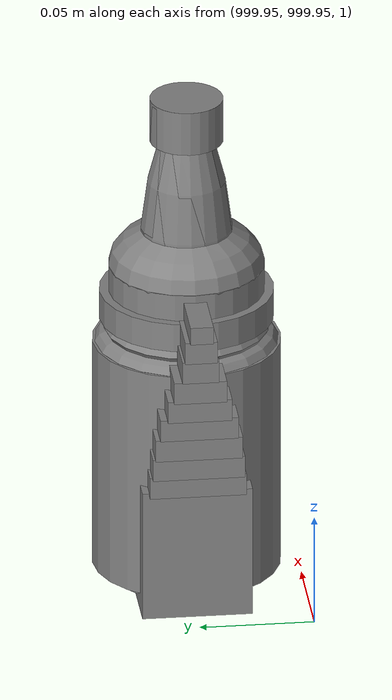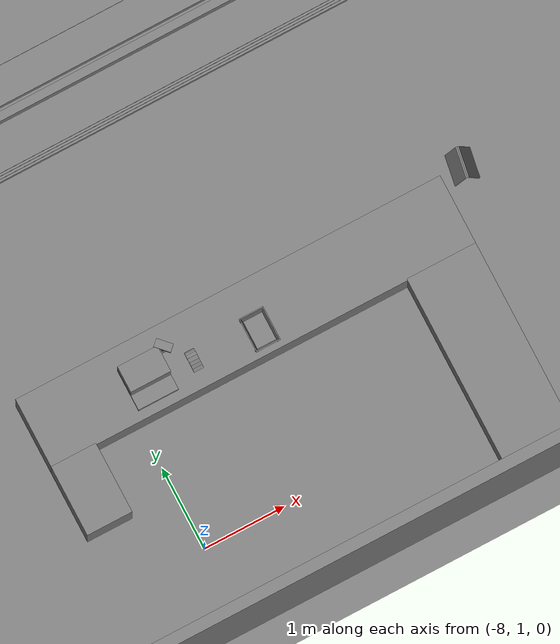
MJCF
<mujoco>
    <option gravity="0.000000000 0.000000000 -9.810000420" timestep="0.0166666" integrator="implicitfast" density="1.225" viscosity="1.8000001e-05" noslip_iterations="10" iterations="100" sdf_iterations="50">
        <flag multiccd="disable"/>
    </option>
    <size memory="1000M"/>
    <compiler coordinate="local"/>
    <worldbody>
        <light cutoff="30" pos="0 1 1" dir="0 -1 -2"/>
        <light cutoff="30" pos="0 -1 1" dir="0 1 -2"/>
        <body pos="0.000000000 0.000000000 0.000000000" euler="0.000000000 0.000000000 0.000000000" name=" Static Objects_ Static Objects">
            <geom contype="1" conaffinity="1" density="1000" type="box" material="" rgba="0.500000000 0.500000000 0.500000000 1.000000000" solimp="0.899999976 0.949999988 0.001000000" friction="1.000000000 0.005000000 0.000100000" solref="0.020000000 1.000000000" margin="0" condim="3" group="0" pos="-3.101639986 6.150595188 1.018643856" quat="1.000000000 0.000000000 0.000000000 0.000000000" size="0.050000001 0.579999983 1.019999981" name=" Static Objects_geom_0E2442DB_9B44_4D3C_9FB1_35723C07D043"/>
            <geom contype="1" conaffinity="1" density="1000" type="box" material="" rgba="0.500000000 0.500000000 0.500000000 1.000000000" solimp="0.899999976 0.949999988 0.001000000" friction="1.000000000 0.005000000 0.000100000" solref="0.020000000 1.000000000" margin="0" condim="3" group="0" pos="-2.825197220 6.153595448 1.115278244" quat="0.707107067 0.000000000 0.000000000 0.707106471" size="0.550000012 0.239999995 0.025000000" name=" Static Objects_geom_1927401C_B0A7_4BE1_88A6_2DB3827D59AB"/>
            <geom contype="1" conaffinity="1" density="1000" type="box" material="" rgba="0.500000000 0.500000000 0.500000000 1.000000000" solimp="0.899999976 0.949999988 0.001000000" friction="1.000000000 0.005000000 0.000100000" solref="0.020000000 1.000000000" margin="0" condim="3" group="0" pos="-2.825197220 6.153595448 0.097434282" quat="0.707107067 0.000000000 0.000000000 0.707106471" size="0.550000012 0.239999995 0.098999999" name=" Static Objects_geom_B115208C_6B74_4650_9877_C27F84827449"/>
            <geom contype="1" conaffinity="1" density="1000" type="box" material="" rgba="0.500000000 0.500000000 0.500000000 1.000000000" solimp="0.899999976 0.949999988 0.001000000" friction="1.000000000 0.005000000 0.000100000" solref="0.020000000 1.000000000" margin="0" condim="3" group="0" pos="-6.293097973 6.153595448 1.114443064" quat="0.707107067 0.000000000 0.000000000 0.707106471" size="0.529999971 3.134999990 0.025000000" name=" Static Objects_geom_8FF8F5F0_362C_4B46_944A_57485A3A526F"/>
            <geom contype="1" conaffinity="1" density="1000" type="box" material="" rgba="0.500000000 0.500000000 0.500000000 1.000000000" solimp="0.899999976 0.949999988 0.001000000" friction="1.000000000 0.005000000 0.000100000" solref="0.020000000 1.000000000" margin="0" condim="3" group="0" pos="-2.825197220 6.153595448 1.563861728" quat="0.707107067 0.000000000 0.000000000 0.707106471" size="0.550000012 0.239999995 0.025000000" name=" Static Objects_geom_56CCDDE2_ED23_4597_9A9D_4588CE75A35A"/>
            <geom contype="1" conaffinity="1" density="1000" type="box" material="" rgba="0.500000000 0.500000000 0.500000000 1.000000000" solimp="0.899999976 0.949999988 0.001000000" friction="1.000000000 0.005000000 0.000100000" solref="0.020000000 1.000000000" margin="0" condim="3" group="0" pos="-6.311686516 6.153595448 1.018643856" quat="0.707107067 0.000000000 0.000000000 0.707106471" size="0.050000001 3.150000095 1.019999981" name=" Static Objects_geom_DBF483C5_A9AB_4EDE_8779_CCE7622ECBD5"/>
            <geom contype="1" conaffinity="1" density="1000" type="box" material="" rgba="0.500000000 0.500000000 0.500000000 1.000000000" solimp="0.899999976 0.949999988 0.001000000" friction="1.000000000 0.005000000 0.000100000" solref="0.020000000 1.000000000" margin="0" condim="3" group="0" pos="-6.286010742 6.153595448 0.096129179" quat="0.707107067 0.000000000 0.000000000 0.707106471" size="0.529999971 3.134999990 0.098999999" name=" Static Objects_geom_29D24D5B_8E35_41A4_8E86_4CF51C5624B0"/>
            <geom contype="1" conaffinity="1" density="1000" type="box" material="" rgba="0.500000000 0.500000000 0.500000000 1.000000000" solimp="0.899999976 0.949999988 0.001000000" friction="1.000000000 0.005000000 0.000100000" solref="0.020000000 1.000000000" margin="0" condim="3" group="0" pos="-2.825197220 6.153595448 0.629031777" quat="0.707107067 0.000000000 0.000000000 0.707106471" size="0.550000012 0.239999995 0.025000000" name=" Static Objects_geom_C9DF8AA7_BABC_49BC_86C6_9561B8BFD26D"/>
            <geom contype="1" conaffinity="1" density="1000" type="box" material="" rgba="0.500000000 0.500000000 0.500000000 1.000000000" solimp="0.899999976 0.949999988 0.001000000" friction="1.000000000 0.005000000 0.000100000" solref="0.020000000 1.000000000" margin="0" condim="3" group="0" pos="-6.286010742 6.153595448 1.563861728" quat="0.707107067 0.000000000 0.000000000 0.707106471" size="0.529999971 3.134999990 0.025000000" name=" Static Objects_geom_5A9379BD_1304_4655_AD41_AB1A49C28470"/>
            <geom contype="1" conaffinity="1" density="1000" type="box" material="" rgba="0.500000000 0.500000000 0.500000000 1.000000000" solimp="0.899999976 0.949999988 0.001000000" friction="1.000000000 0.005000000 0.000100000" solref="0.020000000 1.000000000" margin="0" condim="3" group="0" pos="-6.286010742 6.153595448 0.629031777" quat="0.707107067 0.000000000 0.000000000 0.707106471" size="0.529999971 3.134999990 0.025000000" name=" Static Objects_geom_D15F1E13_3A56_4DD0_B481_78CD5D9C10A8"/>
            <geom contype="1" conaffinity="1" density="1000" type="box" material="" rgba="0.500000000 0.500000000 0.500000000 1.000000000" solimp="0.899999976 0.949999988 0.001000000" friction="1.000000000 0.005000000 0.000100000" solref="0.020000000 1.000000000" margin="0" condim="3" group="0" pos="-7.719123363 2.867671013 1.173410416" quat="1.000000000 0.000000000 0.000000000 0.000000000" size="0.250000000 0.250000000 0.079999998" name=" Static Objects_geom_DD06BD18_506B_4221_8BBF_1C3F45DCA38D"/>
            <geom contype="1" conaffinity="1" density="1000" type="box" material="" rgba="0.500000000 0.500000000 0.500000000 1.000000000" solimp="0.899999976 0.949999988 0.001000000" friction="1.000000000 0.005000000 0.000100000" solref="0.020000000 1.000000000" margin="0" condim="3" group="0" pos="-7.408766270 3.088089943 1.776644945" quat="0.928051054 0.000000000 0.000000000 0.372453064" size="0.050000001 0.100000001 0.050000001" name=" Static Objects_geom_26872344_83B0_4BD2_8AB3_FF477DF2D94F"/>
            <geom contype="1" conaffinity="1" density="1000" type="box" material="" rgba="0.500000000 0.500000000 0.500000000 1.000000000" solimp="0.899999976 0.949999988 0.001000000" friction="1.000000000 0.005000000 0.000100000" solref="0.020000000 1.000000000" margin="0" condim="3" group="0" pos="-7.719123363 2.958004713 1.530241251" quat="1.000000000 0.000000000 0.000000000 0.000000000" size="0.250000000 0.159999996 0.280000001" name=" Static Objects_geom_7EEC0891_91CF_4920_92B4_23B5312A3DD7"/>
            <geom contype="1" conaffinity="1" density="1000" type="cylinder" material="" rgba="0.500000000 0.500000000 0.500000000 1.000000000" solimp="0.899999976 0.949999988 0.001000000" friction="1.000000000 0.005000000 0.000100000" solref="0.020000000 1.000000000" margin="0" condim="3" group="0" pos="-7.427312374 3.069516420 1.502544641" quat="0.928051054 0.000000000 0.000000000 0.372453064" size="0.015000000 0.230000004 0.100000001" name=" Static Objects_geom_37777092_8730_40DA_B0B4_4E7BEE08CC0E"/>
            <geom contype="1" conaffinity="1" density="1000" type="box" material="" rgba="0.500000000 0.500000000 0.500000000 1.000000000" solimp="0.899999976 0.949999988 0.001000000" friction="1.000000000 0.005000000 0.000100000" solref="0.020000000 1.000000000" margin="0" condim="3" group="0" pos="-7.437745571 3.067511320 1.289965630" quat="1.000000000 0.000000000 0.000000000 0.000000000" size="0.029999999 0.020000000 0.020000000" name=" Static Objects_geom_30B6B7C5_DD6C_44FA_A777_AF90E8F4249B"/>
            <geom contype="1" conaffinity="1" density="1000" type="box" material="" rgba="0.500000000 0.500000000 0.500000000 1.000000000" solimp="0.899999976 0.949999988 0.001000000" friction="1.000000000 0.005000000 0.000100000" solref="0.020000000 1.000000000" margin="0" condim="3" group="0" pos="-9.058088303 6.434794426 1.209077358" quat="1.000000000 0.000000000 0.000000000 0.000000000" size="0.250000000 0.100000001 0.070000000" name=" Static Objects_geom_755F766F_6B13_45B3_B7B0_DE5E4C23AB81"/>
            <geom contype="1" conaffinity="1" density="1000" type="box" material="" rgba="0.500000000 0.500000000 0.500000000 1.000000000" solimp="0.899999976 0.949999988 0.001000000" friction="1.000000000 0.005000000 0.000100000" solref="0.020000000 1.000000000" margin="0" condim="3" group="0" pos="-7.886891365 6.459744930 0.352518857" quat="1.000000000 0.000000000 0.000000000 0.000000000" size="1.500000000 0.200000003 0.150000006" name=" Static Objects_geom_CA687A3E_89CF_4FED_8109_385256A10426"/>
            <geom contype="1" conaffinity="1" density="1000" type="box" material="" rgba="0.500000000 0.500000000 0.500000000 1.000000000" solimp="0.899999976 0.949999988 0.001000000" friction="1.000000000 0.005000000 0.000100000" solref="0.020000000 1.000000000" margin="0" condim="3" group="0" pos="-9.237723351 6.464855671 1.209077358" quat="1.000000000 0.000000000 0.000000000 0.000000000" size="0.100000001 0.100000001 0.070000000" name=" Static Objects_geom_DB54987E_F6EB_4539_B95F_10A46ED242A3"/>
            <geom contype="1" conaffinity="1" density="1000" type="box" material="" rgba="0.500000000 0.500000000 0.500000000 1.000000000" solimp="0.899999976 0.949999988 0.001000000" friction="1.000000000 0.005000000 0.000100000" solref="0.020000000 1.000000000" margin="0" condim="3" group="0" pos="-6.924745083 6.362090111 1.214329123" quat="1.000000000 0.000000000 0.000000000 0.000000000" size="0.200000003 0.100000001 0.075000003" name=" Static Objects_geom_6EFD4E1F_4A6B_43FE_8524_1C9C1BAB6534"/>
            <geom contype="1" conaffinity="1" density="1000" type="box" material="" rgba="0.500000000 0.500000000 0.500000000 1.000000000" solimp="0.899999976 0.949999988 0.001000000" friction="1.000000000 0.005000000 0.000100000" solref="0.020000000 1.000000000" margin="0" condim="3" group="0" pos="-4.407354832 6.459744930 1.292199373" quat="1.000000000 0.000000000 0.000000000 0.000000000" size="1.240000010 0.200000003 0.150000006" name=" Static Objects_geom_C7558B3F_DD21_436D_9D60_136D1F1BD197"/>
            <geom contype="1" conaffinity="1" density="1000" type="box" material="" rgba="0.500000000 0.500000000 0.500000000 1.000000000" solimp="0.899999976 0.949999988 0.001000000" friction="1.000000000 0.005000000 0.000100000" solref="0.020000000 1.000000000" margin="0" condim="3" group="0" pos="-5.611940861 6.318420410 0.350975692" quat="1.000000000 0.000000000 0.000000000 0.000000000" size="0.699999988 0.100000001 0.150000006" name=" Static Objects_geom_5FDB6F21_4034_4AAA_B5E4_BE9A0A2A3F87"/>
            <geom contype="1" conaffinity="1" density="1000" type="box" material="" rgba="0.500000000 0.500000000 0.500000000 1.000000000" solimp="0.899999976 0.949999988 0.001000000" friction="1.000000000 0.005000000 0.000100000" solref="0.020000000 1.000000000" margin="0" condim="3" group="0" pos="-6.300771236 6.459744930 1.744376063" quat="1.000000000 0.000000000 0.000000000 0.000000000" size="3.000000000 0.200000003 0.150000006" name=" Static Objects_geom_CF016476_A108_4C69_93AC_D2759D69D3F4"/>
            <geom contype="1" conaffinity="1" density="1000" type="box" material="" rgba="0.500000000 0.500000000 0.500000000 1.000000000" solimp="0.899999976 0.949999988 0.001000000" friction="1.000000000 0.005000000 0.000100000" solref="0.020000000 1.000000000" margin="0" condim="3" group="0" pos="-8.844120979 6.464855671 1.209077358" quat="1.000000000 0.000000000 0.000000000 0.000000000" size="0.100000001 0.100000001 0.070000000" name=" Static Objects_geom_394FE816_3E7C_4B5E_B596_5B0EC76CCFD1"/>
            <geom contype="1" conaffinity="1" density="1000" type="box" material="" rgba="0.500000000 0.500000000 0.500000000 1.000000000" solimp="0.899999976 0.949999988 0.001000000" friction="1.000000000 0.005000000 0.000100000" solref="0.020000000 1.000000000" margin="0" condim="3" group="0" pos="-6.824534416 6.447464466 1.212718010" quat="1.000000000 0.000000000 0.000000000 0.000000000" size="0.100000001 0.100000001 0.075000003" name=" Static Objects_geom_9C49C489_BA99_4973_83EE_C9E342A2C4FB"/>
            <geom contype="1" conaffinity="1" density="1000" type="box" material="" rgba="0.500000000 0.500000000 0.500000000 1.000000000" solimp="0.899999976 0.949999988 0.001000000" friction="1.000000000 0.005000000 0.000100000" solref="0.020000000 1.000000000" margin="0" condim="3" group="0" pos="-6.751636982 6.459744930 0.800981164" quat="1.000000000 0.000000000 0.000000000 0.000000000" size="2.200000048 0.200000003 0.150000006" name=" Static Objects_geom_0D5F06E2_E4C1_4D6E_B9AE_20DA45FD3B91"/>
            <geom contype="1" conaffinity="1" density="1000" type="box" material="" rgba="0.500000000 0.500000000 0.500000000 1.000000000" solimp="0.899999976 0.949999988 0.001000000" friction="1.000000000 0.005000000 0.000100000" solref="0.020000000 1.000000000" margin="0" condim="3" group="0" pos="-6.098561764 6.327973843 1.292199373" quat="1.000000000 0.000000000 0.000000000 0.000000000" size="0.500000000 0.100000001 0.150000006" name=" Static Objects_geom_6613A271_A621_47C4_AA22_783A16F3DD9E"/>
            <geom contype="1" conaffinity="1" density="1000" type="box" material="" rgba="0.500000000 0.500000000 0.500000000 1.000000000" solimp="0.899999976 0.949999988 0.001000000" friction="1.000000000 0.005000000 0.000100000" solref="0.020000000 1.000000000" margin="0" condim="3" group="0" pos="-3.907610416 6.318625927 0.800981164" quat="1.000000000 0.000000000 0.000000000 0.000000000" size="0.500000000 0.100000001 0.150000006" name=" Static Objects_geom_C99E5626_3099_4837_9EB8_C0C7CFD12868"/>
            <geom contype="1" conaffinity="1" density="1000" type="box" material="" rgba="0.500000000 0.500000000 0.500000000 1.000000000" solimp="0.899999976 0.949999988 0.001000000" friction="1.000000000 0.005000000 0.000100000" solref="0.020000000 1.000000000" margin="0" condim="3" group="0" pos="-7.373087406 6.458900928 1.214329123" quat="1.000000000 0.000000000 0.000000000 0.000000000" size="0.250000000 0.200000003 0.075000003" name=" Static Objects_geom_00B02C0E_7E82_426F_A8A7_15CB123BFCA3"/>
            <geom contype="1" conaffinity="1" density="1000" type="box" material="" rgba="0.500000000 0.500000000 0.500000000 1.000000000" solimp="0.899999976 0.949999988 0.001000000" friction="1.000000000 0.005000000 0.000100000" solref="0.020000000 1.000000000" margin="0" condim="3" group="0" pos="-4.035642624 6.459744930 0.352518857" quat="1.000000000 0.000000000 0.000000000 0.000000000" size="0.800000012 0.200000003 0.150000006" name=" Static Objects_geom_99156728_2163_4264_A03B_C7E2C1D7AFBF"/>
            <geom contype="1" conaffinity="1" density="1000" type="box" material="" rgba="0.500000000 0.500000000 0.500000000 1.000000000" solimp="0.899999976 0.949999988 0.001000000" friction="1.000000000 0.005000000 0.000100000" solref="0.020000000 1.000000000" margin="0" condim="3" group="0" pos="-6.460197449 2.937205315 0.548931718" quat="1.000000000 0.000000000 0.000000000 0.000000000" size="2.650000095 0.430000007 0.550000012" name=" Static Objects_geom_9FCA6D1D_B532_412C_862C_A1EDDDBAB5AD"/>
            <geom contype="1" conaffinity="1" density="1000" type="box" material="" rgba="0.500000000 0.500000000 0.500000000 1.000000000" solimp="0.899999976 0.949999988 0.001000000" friction="1.000000000 0.005000000 0.000100000" solref="0.020000000 1.000000000" margin="0" condim="3" group="0" pos="-4.240264893 1.327049494 0.549888909" quat="1.000000000 0.000000000 0.000000000 0.000000000" size="0.430000007 1.200000048 0.550000012" name=" Static Objects_geom_C485BED5_4193_4041_A0A3_AC2ABA1C1A3C"/>
            <geom contype="1" conaffinity="1" density="1000" type="box" material="" rgba="0.500000000 0.500000000 0.500000000 1.000000000" solimp="0.899999976 0.949999988 0.001000000" friction="1.000000000 0.005000000 0.000100000" solref="0.020000000 1.000000000" margin="0" condim="3" group="0" pos="-8.830721855 2.096410990 0.549305558" quat="1.000000000 0.000000000 0.000000000 0.000000000" size="0.280000001 0.430000007 0.550000012" name=" Static Objects_geom_0C6AF3D5_61B7_4556_809A_AA0BA1B7D7AD"/>
            <geom contype="1" conaffinity="1" density="1000" type="plane" material="" rgba="0.500000000 0.500000000 0.500000000 1.000000000" solimp="0.899999976 0.949999988 0.001000000" friction="1.000000000 0.005000000 0.000100000" solref="0.020000000 1.000000000" margin="0" condim="3" group="0" pos="-6.000000000 10.399999619 0.000000000" quat="1.000000000 0.000000000 0.000000000 0.000000000" size="6.050000191 10.800000191 0.010000000" name=" Static Objects_geom_AFC58E39_76E4_429A_9432_770C43511B49"/>
            <geom contype="1" conaffinity="1" density="1000" type="box" material="" rgba="0.500000000 0.500000000 0.500000000 1.000000000" solimp="0.899999976 0.949999988 0.001000000" friction="1.000000000 0.005000000 0.000100000" solref="0.020000000 1.000000000" margin="0" condim="3" group="0" pos="-6.000000000 0.035000000 2.000000000" quat="1.000000000 0.000000000 0.000000000 0.000000000" size="6.079999924 0.070000000 2.000000000" name=" Static Objects_geom_75C3CFDC_6CE1_4D94_82A9_ABFA868258A9"/>
            <geom contype="1" conaffinity="1" density="1000" type="box" material="" rgba="0.500000000 0.500000000 0.500000000 1.000000000" solimp="0.899999976 0.949999988 0.001000000" friction="1.000000000 0.005000000 0.000100000" solref="0.020000000 1.000000000" margin="0" condim="3" group="0" pos="-6.000000000 20.159999847 2.000000000" quat="1.000000000 0.000000000 0.000000000 0.000000000" size="6.079999924 0.070000000 2.000000000" name=" Static Objects_geom_3818D0E4_96FC_4249_854F_49866A7EED20"/>
            <geom contype="1" conaffinity="1" density="1000" type="box" material="" rgba="0.500000000 0.500000000 0.500000000 1.000000000" solimp="0.899999976 0.949999988 0.001000000" friction="1.000000000 0.005000000 0.000100000" solref="0.020000000 1.000000000" margin="0" condim="3" group="0" pos="0.000000000 10.000000000 2.000000000" quat="1.000000000 0.000000000 0.000000000 0.000000000" size="0.070000000 10.500000000 2.000000000" name=" Static Objects_geom_5D4D8DCE_DAB3_4DEB_A765_90B2FF6F3CA1"/>
            <geom contype="1" conaffinity="1" density="1000" type="box" material="" rgba="0.500000000 0.500000000 0.500000000 1.000000000" solimp="0.899999976 0.949999988 0.001000000" friction="1.000000000 0.005000000 0.000100000" solref="0.020000000 1.000000000" margin="0" condim="3" group="0" pos="-12.050000191 10.000000000 2.000000000" quat="1.000000000 0.000000000 0.000000000 0.000000000" size="0.070000000 10.500000000 2.000000000" name=" Static Objects_geom_36B07BC4_1ADC_46BC_8486_488EC162D87B"/>
        </body>
        <body pos="1000.000000000 1000.000000000 1.000000000" euler="0.000000000 0.000000000 0.000000000" name="openloong_gripper_2f85_fix_base_usda_can">
            <geom contype="1" conaffinity="1" density="1000" type="cylinder" material="" rgba="0.500000000 0.500000000 0.500000000 1.000000000" solimp="0.899999976 0.949999988 0.001000000" friction="1.000000000 0.005000000 0.000100000" solref="0.020000000 1.000000000" margin="0" condim="3" group="0" pos="0.000000000 0.000000000 0.079676986" quat="1.000000000 0.000000000 0.000000000 0.000000000" size="0.034000002 0.071999997 1.000000000" name="openloong_gripper_2f85_fix_base_usda_geom_8A3859B2_84EF_4523_B408_F29A1149685B"/>
            <geom contype="1" conaffinity="1" density="1000" type="ellipsoid" material="" rgba="0.500000000 0.500000000 0.500000000 1.000000000" solimp="0.899999976 0.949999988 0.001000000" friction="1.000000000 0.005000000 0.000100000" solref="0.020000000 1.000000000" margin="0" condim="3" group="0" pos="0.000000000 0.000000000 0.151854277" quat="1.000000000 0.000000000 0.000000000 0.000000000" size="0.034000002 0.034000002 0.020000000" name="openloong_gripper_2f85_fix_base_usda_geom_6497CE56_1682_4DD4_B82A_C5E5D73C3B5B"/>
            <geom contype="1" conaffinity="1" density="1000" type="box" material="" rgba="0.500000000 0.500000000 0.500000000 1.000000000" solimp="0.899999976 0.949999988 0.001000000" friction="1.000000000 0.005000000 0.000100000" solref="0.020000000 1.000000000" margin="0" condim="3" group="0" pos="0.000000000 0.000000000 0.004777670" quat="1.000000000 0.000000000 0.000000000 0.000000000" size="0.020000000 0.020000000 0.005000000" name="openloong_gripper_2f85_fix_base_usda_geom_8D141EFB_1E54_4A03_94AE_DBD913408BC8"/>
            <freejoint name="openloong_gripper_2f85_fix_base_usda_can_joint"/>
            <site size="0.005000000 0.005000000 0.005000000" rgba="0.500000000 0.500000000 0.500000000 1.000000000" pos="0.000000000 0.000000000 0.000000000" quat="1.000000000 0.000000000 0.000000000 0.000000000" group="0" type="sphere" name="openloong_gripper_2f85_fix_base_usda_cansite"/>
        </body>
        <body pos="1000.000000000 1000.000000000 1.000000000" euler="0.000000000 0.000000000 0.000000000" name="openloong_gripper_2f85_fix_base_usda_jar_01">
            <geom contype="1" conaffinity="1" density="1000" type="box" material="" rgba="0.500000000 0.500000000 0.500000000 1.000000000" solimp="0.899999976 0.949999988 0.001000000" friction="1.000000000 0.005000000 0.000100000" solref="0.020000000 1.000000000" margin="0" condim="3" group="0" pos="0.000000000 0.000000000 0.006158113" quat="1.000000000 0.000000000 0.000000000 0.000000000" size="0.020000000 0.020000000 0.005000000" name="openloong_gripper_2f85_fix_base_usda_geom_757EDF1B_B9DF_4F97_9C96_0E889F6214D4"/>
            <geom contype="1" conaffinity="1" density="1000" type="cylinder" material="" rgba="0.500000000 0.500000000 0.500000000 1.000000000" solimp="0.899999976 0.949999988 0.001000000" friction="1.000000000 0.005000000 0.000100000" solref="0.020000000 1.000000000" margin="0" condim="3" group="0" pos="0.000000000 0.000000000 0.062744498" quat="1.000000000 0.000000000 0.000000000 0.000000000" size="0.041000001 0.052999999 1.000000000" name="openloong_gripper_2f85_fix_base_usda_geom_8E102295_6AC4_4597_93CF_21D6FE4AA425"/>
            <geom contype="1" conaffinity="1" density="1000" type="ellipsoid" material="" rgba="0.500000000 0.500000000 0.500000000 1.000000000" solimp="0.899999976 0.949999988 0.001000000" friction="1.000000000 0.005000000 0.000100000" solref="0.020000000 1.000000000" margin="0" condim="3" group="0" pos="0.000000000 0.000000000 0.122252703" quat="1.000000000 0.000000000 0.000000000 0.000000000" size="0.035999998 0.035999998 0.010000000" name="openloong_gripper_2f85_fix_base_usda_geom_CB2B7CAF_866C_4400_AC5C_4FD329D80D0E"/>
            <geom contype="1" conaffinity="1" density="1000" type="cylinder" material="" rgba="0.500000000 0.500000000 0.500000000 1.000000000" solimp="0.899999976 0.949999988 0.001000000" friction="1.000000000 0.005000000 0.000100000" solref="0.020000000 1.000000000" margin="0" condim="3" group="0" pos="0.000000000 0.000000000 0.015747190" quat="1.000000000 0.000000000 0.000000000 0.000000000" size="0.035000000 0.010000000 1.000000000" name="openloong_gripper_2f85_fix_base_usda_geom_C1D6967A_32F2_47AE_9B38_B036EF70F054"/>
            <geom contype="1" conaffinity="1" density="1000" type="ellipsoid" material="" rgba="0.500000000 0.500000000 0.500000000 1.000000000" solimp="0.899999976 0.949999988 0.001000000" friction="1.000000000 0.005000000 0.000100000" solref="0.020000000 1.000000000" margin="0" condim="3" group="0" pos="0.000000000 0.000000000 0.115815401" quat="1.000000000 0.000000000 0.000000000 0.000000000" size="0.039999999 0.039999999 0.010000000" name="openloong_gripper_2f85_fix_base_usda_geom_2F3984CE_72C7_4EDB_A0E0_F8DCDE04A30B"/>
            <geom contype="1" conaffinity="1" density="1000" type="cylinder" material="" rgba="0.500000000 0.500000000 0.500000000 1.000000000" solimp="0.899999976 0.949999988 0.001000000" friction="1.000000000 0.005000000 0.000100000" solref="0.020000000 1.000000000" margin="0" condim="3" group="0" pos="0.000000000 0.000000000 0.133183479" quat="1.000000000 0.000000000 0.000000000 0.000000000" size="0.037999999 0.006500000 1.000000000" name="openloong_gripper_2f85_fix_base_usda_geom_B6F40FAE_82DF_4D12_A6A3_D181CDB47AFE"/>
            <freejoint name="openloong_gripper_2f85_fix_base_usda_jar_01_joint"/>
            <site size="0.005000000 0.005000000 0.005000000" rgba="0.500000000 0.500000000 0.500000000 1.000000000" pos="0.000000000 0.000000000 0.000000000" quat="1.000000000 0.000000000 0.000000000 0.000000000" group="0" type="sphere" name="openloong_gripper_2f85_fix_base_usda_jar_01site"/>
        </body>
        <body pos="1000.000000000 1000.000000000 1.000000000" euler="0.000000000 0.000000000 0.000000000" name="openloong_gripper_2f85_fix_base_usda_salt">
            <geom contype="1" conaffinity="1" density="1000" type="box" material="" rgba="0.500000000 0.500000000 0.500000000 1.000000000" solimp="0.899999976 0.949999988 0.001000000" friction="1.000000000 0.005000000 0.000100000" solref="0.020000000 1.000000000" margin="0" condim="3" group="0" pos="0.000305176 0.000000000 0.084862232" quat="1.000000000 0.000000000 0.000000000 0.000000000" size="0.048999999 0.018999999 0.005000000" name="openloong_gripper_2f85_fix_base_usda_geom_73453B80_355D_478B_9860_7D0FF4AB3DA7"/>
            <geom contype="1" conaffinity="1" density="1000" type="box" material="" rgba="0.500000000 0.500000000 0.500000000 1.000000000" solimp="0.899999976 0.949999988 0.001000000" friction="1.000000000 0.005000000 0.000100000" solref="0.020000000 1.000000000" margin="0" condim="3" group="0" pos="0.000305176 0.000000000 0.104564309" quat="1.000000000 0.000000000 0.000000000 0.000000000" size="0.052000001 0.014000000 0.005000000" name="openloong_gripper_2f85_fix_base_usda_geom_EEAD2950_5C15_4194_AB43_ECEF5D71212A"/>
            <geom contype="1" conaffinity="1" density="1000" type="box" material="" rgba="0.500000000 0.500000000 0.500000000 1.000000000" solimp="0.899999976 0.949999988 0.001000000" friction="1.000000000 0.005000000 0.000100000" solref="0.020000000 1.000000000" margin="0" condim="3" group="0" pos="0.000305176 0.000000000 0.114487171" quat="1.000000000 0.000000000 0.000000000 0.000000000" size="0.054000001 0.011500000 0.005000000" name="openloong_gripper_2f85_fix_base_usda_geom_E8C4A7FC_622C_40D9_AB2E_7F4A02F397C2"/>
            <geom contype="1" conaffinity="1" density="1000" type="box" material="" rgba="0.500000000 0.500000000 0.500000000 1.000000000" solimp="0.899999976 0.949999988 0.001000000" friction="1.000000000 0.005000000 0.000100000" solref="0.020000000 1.000000000" margin="0" condim="3" group="0" pos="0.000305176 0.000000000 0.075103164" quat="1.000000000 0.000000000 0.000000000 0.000000000" size="0.048000000 0.020000000 0.005000000" name="openloong_gripper_2f85_fix_base_usda_geom_ECEA2ED7_BEC6_499D_A9E6_9D017DCF57E3"/>
            <geom contype="1" conaffinity="1" density="1000" type="box" material="" rgba="0.500000000 0.500000000 0.500000000 1.000000000" solimp="0.899999976 0.949999988 0.001000000" friction="1.000000000 0.005000000 0.000100000" solref="0.020000000 1.000000000" margin="0" condim="3" group="0" pos="0.000305176 0.000000000 0.134892464" quat="1.000000000 0.000000000 0.000000000 0.000000000" size="0.057000000 0.007000000 0.005000000" name="openloong_gripper_2f85_fix_base_usda_geom_096031F3_D61C_4C54_BA71_59D9A988412E"/>
            <geom contype="1" conaffinity="1" density="1000" type="box" material="" rgba="0.500000000 0.500000000 0.500000000 1.000000000" solimp="0.899999976 0.949999988 0.001000000" friction="1.000000000 0.005000000 0.000100000" solref="0.020000000 1.000000000" margin="0" condim="3" group="0" pos="0.000305176 0.000000000 0.094920278" quat="1.000000000 0.000000000 0.000000000 0.000000000" size="0.050000001 0.017000001 0.005000000" name="openloong_gripper_2f85_fix_base_usda_geom_6A66C418_0317_4995_BF71_8A01D8053B5D"/>
            <geom contype="1" conaffinity="1" density="1000" type="box" material="" rgba="0.500000000 0.500000000 0.500000000 1.000000000" solimp="0.899999976 0.949999988 0.001000000" friction="1.000000000 0.005000000 0.000100000" solref="0.020000000 1.000000000" margin="0" condim="3" group="0" pos="0.000305176 0.000000000 0.065204859" quat="1.000000000 0.000000000 0.000000000 0.000000000" size="0.045000002 0.021000000 0.005000000" name="openloong_gripper_2f85_fix_base_usda_geom_73CFF3D8_A2B2_4311_B31C_4024EE92DE14"/>
            <geom contype="1" conaffinity="1" density="1000" type="box" material="" rgba="0.500000000 0.500000000 0.500000000 1.000000000" solimp="0.899999976 0.949999988 0.001000000" friction="1.000000000 0.005000000 0.000100000" solref="0.020000000 1.000000000" margin="0" condim="3" group="0" pos="0.000305176 0.000000000 0.144135714" quat="1.000000000 0.000000000 0.000000000 0.000000000" size="0.059000000 0.005000000 0.004000000" name="openloong_gripper_2f85_fix_base_usda_geom_ABF64FE5_B230_4EF5_B17B_E4BFDD372237"/>
            <geom contype="1" conaffinity="1" density="1000" type="box" material="" rgba="0.500000000 0.500000000 0.500000000 1.000000000" solimp="0.899999976 0.949999988 0.001000000" friction="1.000000000 0.005000000 0.000100000" solref="0.020000000 1.000000000" margin="0" condim="3" group="0" pos="0.000000000 0.000000000 0.031593561" quat="1.000000000 0.000000000 0.000000000 0.000000000" size="0.041999999 0.024000000 0.029999999" name="openloong_gripper_2f85_fix_base_usda_geom_26EB9FE5_35A5_4888_A567_E3762C2F9010"/>
            <geom contype="1" conaffinity="1" density="1000" type="box" material="" rgba="0.500000000 0.500000000 0.500000000 1.000000000" solimp="0.899999976 0.949999988 0.001000000" friction="1.000000000 0.005000000 0.000100000" solref="0.020000000 1.000000000" margin="0" condim="3" group="0" pos="0.000305176 0.000000000 0.124608755" quat="1.000000000 0.000000000 0.000000000 0.000000000" size="0.055000000 0.008000000 0.005000000" name="openloong_gripper_2f85_fix_base_usda_geom_9670C5E4_A421_4E0A_B951_C447CBDA7F8D"/>
            <freejoint name="openloong_gripper_2f85_fix_base_usda_salt_joint"/>
            <site size="0.005000000 0.005000000 0.005000000" rgba="0.500000000 0.500000000 0.500000000 1.000000000" pos="0.000000000 0.000000000 0.000000000" quat="1.000000000 0.000000000 0.000000000 0.000000000" group="0" type="sphere" name="openloong_gripper_2f85_fix_base_usda_saltsite"/>
        </body>
        <body pos="-2.162051201 5.824904919 1.710306883" euler="72.164077759 -40.098274231 -125.770057678" mocap="true" name="spotlight2_SpotLight"/>
        <body pos="-1.962047577 6.438086033 1.853903770" euler="74.631462097 -51.471443176 156.739013672" mocap="true" name="spotlight1_SpotLight"/>
        <body pos="1000.000000000 1000.000000000 1.000000000" euler="0.000000000 0.000000000 0.000000000" name="openloong_gripper_2f85_fix_base_usda_bottle_blue">
            <geom contype="1" conaffinity="1" density="1000" type="ellipsoid" material="" rgba="0.500000000 0.500000000 0.500000000 1.000000000" solimp="0.899999976 0.949999988 0.001000000" friction="1.000000000 0.005000000 0.000100000" solref="0.020000000 1.000000000" margin="0" condim="3" group="0" pos="0.000000000 0.000000000 0.118920922" quat="1.000000000 0.000000000 0.000000000 0.000000000" size="0.030999999 0.030999999 0.029999999" name="openloong_gripper_2f85_fix_base_usda_geom_A979D4DA_2036_4BBC_B835_A7603E90C1EA"/>
            <geom contype="1" conaffinity="1" density="1000" type="box" material="" rgba="0.500000000 0.500000000 0.500000000 1.000000000" solimp="0.899999976 0.949999988 0.001000000" friction="1.000000000 0.005000000 0.000100000" solref="0.020000000 1.000000000" margin="0" condim="3" group="0" pos="0.000000000 0.000000000 0.002164602" quat="1.000000000 0.000000000 0.000000000 0.000000000" size="0.020000000 0.020000000 0.003000000" name="openloong_gripper_2f85_fix_base_usda_geom_93446B6D_EFDC_4C63_B442_546F625D8D28"/>
            <geom contype="1" conaffinity="1" density="1000" type="cylinder" material="" rgba="0.500000000 0.500000000 0.500000000 1.000000000" solimp="0.899999976 0.949999988 0.001000000" friction="1.000000000 0.005000000 0.000100000" solref="0.020000000 1.000000000" margin="0" condim="3" group="0" pos="0.000000000 -0.000366211 0.060859680" quat="1.000000000 0.000000000 0.000000000 0.000000000" size="0.030999999 0.057999998 1.000000000" name="openloong_gripper_2f85_fix_base_usda_geom_12224CEC_3CFC_4E33_8759_7FEFA713DD92"/>
            <geom contype="1" conaffinity="1" density="1000" type="cylinder" material="" rgba="0.500000000 0.500000000 0.500000000 1.000000000" solimp="0.899999976 0.949999988 0.001000000" friction="1.000000000 0.005000000 0.000100000" solref="0.020000000 1.000000000" margin="0" condim="3" group="0" pos="0.000000000 0.000000000 0.220594406" quat="1.000000000 0.000000000 0.000000000 0.000000000" size="0.016000001 0.010000000 1.000000000" name="openloong_gripper_2f85_fix_base_usda_geom_42185C83_37A5_4AD0_9AF0_EEAEDC325128"/>
            <geom contype="1" conaffinity="1" density="1000" type="ellipsoid" material="" rgba="0.500000000 0.500000000 0.500000000 1.000000000" solimp="0.899999976 0.949999988 0.001000000" friction="1.000000000 0.005000000 0.000100000" solref="0.020000000 1.000000000" margin="0" condim="3" group="0" pos="0.000000000 0.000000000 0.144259930" quat="1.000000000 0.000000000 0.000000000 0.000000000" size="0.021000000 0.021000000 0.079999998" name="openloong_gripper_2f85_fix_base_usda_geom_9B3C96BF_2C97_4F42_A09A_CAD5538BD8D5"/>
            <freejoint name="openloong_gripper_2f85_fix_base_usda_bottle_blue_joint"/>
            <site size="0.005000000 0.005000000 0.005000000" rgba="0.500000000 0.500000000 0.500000000 1.000000000" pos="0.000000000 0.000000000 0.000000000" quat="0.999961913 0.008726535 0.000000000 0.000000000" group="0" type="sphere" name="openloong_gripper_2f85_fix_base_usda_bottle_bluesite"/>
        </body>
        <body pos="-1.826377392 5.995862007 1.721085191" euler="-64.371101379 67.841270447 134.035079956" mocap="true" name="spotlight6_SpotLight"/>
        <body pos="1000.000000000 1000.000000000 1.000000000" euler="0.000000000 0.000000000 0.000000000" name="openloong_gripper_2f85_fix_base_usda_bottle_red">
            <geom contype="1" conaffinity="1" density="1000" type="ellipsoid" material="" rgba="0.500000000 0.500000000 0.500000000 1.000000000" solimp="0.899999976 0.949999988 0.001000000" friction="1.000000000 0.005000000 0.000100000" solref="0.020000000 1.000000000" margin="0" condim="3" group="0" pos="0.000000000 0.000000000 0.144284487" quat="1.000000000 0.000000000 0.000000000 0.000000000" size="0.021000000 0.021000000 0.079999998" name="openloong_gripper_2f85_fix_base_usda_geom_A14B0478_CBA3_432F_90CC_EDF4D5831510"/>
            <geom contype="1" conaffinity="1" density="1000" type="cylinder" material="" rgba="0.500000000 0.500000000 0.500000000 1.000000000" solimp="0.899999976 0.949999988 0.001000000" friction="1.000000000 0.005000000 0.000100000" solref="0.020000000 1.000000000" margin="0" condim="3" group="0" pos="0.000000000 0.000000000 0.220618963" quat="1.000000000 0.000000000 0.000000000 0.000000000" size="0.016000001 0.010000000 1.000000000" name="openloong_gripper_2f85_fix_base_usda_geom_57701306_0C86_41EE_9B6C_20D4B760BF93"/>
            <geom contype="1" conaffinity="1" density="1000" type="ellipsoid" material="" rgba="0.500000000 0.500000000 0.500000000 1.000000000" solimp="0.899999976 0.949999988 0.001000000" friction="1.000000000 0.005000000 0.000100000" solref="0.020000000 1.000000000" margin="0" condim="3" group="0" pos="0.000000000 0.000000000 0.118945479" quat="1.000000000 0.000000000 0.000000000 0.000000000" size="0.030999999 0.030999999 0.029999999" name="openloong_gripper_2f85_fix_base_usda_geom_BFD1F927_7306_49F8_90AD_6D9F15A35670"/>
            <geom contype="1" conaffinity="1" density="1000" type="box" material="" rgba="0.500000000 0.500000000 0.500000000 1.000000000" solimp="0.899999976 0.949999988 0.001000000" friction="1.000000000 0.005000000 0.000100000" solref="0.020000000 1.000000000" margin="0" condim="3" group="0" pos="0.000000000 0.000000000 0.002189159" quat="1.000000000 0.000000000 0.000000000 0.000000000" size="0.020000000 0.020000000 0.003000000" name="openloong_gripper_2f85_fix_base_usda_geom_8213BDF6_6B1D_45CC_83AF_5A86906ABA5A"/>
            <geom contype="1" conaffinity="1" density="1000" type="cylinder" material="" rgba="0.500000000 0.500000000 0.500000000 1.000000000" solimp="0.899999976 0.949999988 0.001000000" friction="1.000000000 0.005000000 0.000100000" solref="0.020000000 1.000000000" margin="0" condim="3" group="0" pos="0.000000000 -0.000366211 0.060884237" quat="1.000000000 0.000000000 0.000000000 0.000000000" size="0.030999999 0.057999998 1.000000000" name="openloong_gripper_2f85_fix_base_usda_geom_95F0DBEE_A4AF_4314_BDCE_BB67AB901896"/>
            <freejoint name="openloong_gripper_2f85_fix_base_usda_bottle_red_joint"/>
            <site size="0.005000000 0.005000000 0.005000000" rgba="0.500000000 0.500000000 0.500000000 1.000000000" pos="0.000000000 0.000000000 0.000000000" quat="0.999961913 0.008726535 0.000000000 0.000000000" group="0" type="sphere" name="openloong_gripper_2f85_fix_base_usda_bottle_redsite"/>
        </body>
        <body pos="0.000000000 0.000000000 0.000000000" euler="0.000000000 0.000000000 0.000000000" name="Interactive Objects_Interactive Objects"/>
        <body pos="-3.510578632 3.403555870 -0.000000100" euler="0.000000000 0.000000000 40.200675964" name="openloong_gripper_2f85_fix_base_usda_PZ">
            <geom contype="1" conaffinity="1" density="1000" type="box" material="" rgba="0.500000000 0.500000000 0.500000000 1.000000000" solimp="0.899999976 0.949999988 0.001000000" friction="1.000000000 0.005000000 0.000100000" solref="0.020000000 1.000000000" margin="0" condim="3" group="0" pos="-0.047453165 0.056484699 0.373715430" quat="0.934750080 0.077914521 0.028795123 0.345459938" size="0.180000007 0.010000000 0.379999995" name="openloong_gripper_2f85_fix_base_usda_geom_6CBCB955_620D_4921_A6AC_8D1D0028A8ED"/>
            <geom contype="1" conaffinity="1" density="1000" type="box" material="" rgba="0.500000000 0.500000000 0.500000000 1.000000000" solimp="0.899999976 0.949999988 0.001000000" friction="1.000000000 0.005000000 0.000100000" solref="0.020000000 1.000000000" margin="0" condim="3" group="0" pos="0.047452450 -0.054376602 0.374072611" quat="0.934387863 -0.082143910 -0.030358355 0.345326364" size="0.180000007 0.010000000 0.379999995" name="openloong_gripper_2f85_fix_base_usda_geom_14745588_74B1_4142_8AAE_24F0F9D7DB74"/>
            <freejoint name="openloong_gripper_2f85_fix_base_usda_PZ"/>
        </body>
        <body pos="-6.332345009 2.779978037 1.034067392" euler="0.000000000 0.000000000 0.000000000" name="openloong_gripper_2f85_fix_base_usda_basket">
            <geom contype="1" conaffinity="1" density="100000" type="box" material="" rgba="0.500000000 0.500000000 0.500000000 1.000000000" solimp="0.899999976 0.949999988 0.001000000" friction="1.000000000 0.899999976 0.000100000" solref="0.020000000 1.000000000" margin="0" condim="3" group="0" pos="-0.172339439 0.000000000 0.168361664" quat="0.706172407 -0.036353018 -0.036353093 0.706170976" size="0.200000003 0.006000000 0.108000003" name="openloong_gripper_2f85_fix_base_usda_geom_6F92835E_54F4_4E67_BA30_1CF5FB24B51F"/>
            <geom contype="1" conaffinity="1" density="100000" type="box" material="" rgba="0.500000000 0.500000000 0.500000000 1.000000000" solimp="0.899999976 0.949999988 0.001000000" friction="1.000000000 0.899999976 0.000100000" solref="0.020000000 1.000000000" margin="0" condim="3" group="0" pos="-0.039724827 -0.188568115 0.167089701" quat="0.997537494 0.070135131 0.000000000 0.000000000" size="0.150000006 0.006000000 0.108000003" name="openloong_gripper_2f85_fix_base_usda_geom_1C8E61C0_7F46_4294_B809_218162C90C63"/>
            <geom contype="1" conaffinity="1" density="100000" type="box" material="" rgba="0.500000000 0.500000000 0.500000000 1.000000000" solimp="0.899999976 0.949999988 0.001000000" friction="1.000000000 0.899999976 0.000100000" solref="0.020000000 1.000000000" margin="0" condim="3" group="0" pos="-0.039724827 0.188377380 0.167089701" quat="0.997489929 -0.070808925 0.000000000 0.000000000" size="0.150000006 0.006000000 0.108000003" name="openloong_gripper_2f85_fix_base_usda_geom_B2F3E4E8_661B_4D94_9F44_87A4A2B16ABD"/>
            <geom contype="1" conaffinity="1" density="100000" type="box" material="" rgba="0.500000000 0.500000000 0.500000000 1.000000000" solimp="0.899999976 0.949999988 0.001000000" friction="1.000000000 0.899999976 0.000100000" solref="0.020000000 1.000000000" margin="0" condim="3" group="0" pos="-0.039724827 0.000000000 0.068126202" quat="1.000000000 0.000000000 0.000000000 0.000000000" size="0.129999995 0.174999997 0.006000000" name="openloong_gripper_2f85_fix_base_usda_geom_8D59C85A_AE84_4ACE_9774_7812FAD496C3"/>
            <geom contype="1" conaffinity="1" density="100000" type="box" material="" rgba="0.500000000 0.500000000 0.500000000 1.000000000" solimp="0.899999976 0.949999988 0.001000000" friction="1.000000000 0.899999976 0.000100000" solref="0.020000000 1.000000000" margin="0" condim="3" group="0" pos="0.094372749 0.000000000 0.168361664" quat="0.706172049 0.036353335 0.036353379 0.706171215" size="0.200000003 0.006000000 0.108000003" name="openloong_gripper_2f85_fix_base_usda_geom_0AF7453E_1F8B_45D7_9985_8A316470B752"/>
            <freejoint name="openloong_gripper_2f85_fix_base_usda_basket_joint"/>
            <site size="0.005000000 0.005000000 0.005000000" rgba="0.500000000 0.500000000 0.500000000 1.000000000" pos="0.000000000 0.000000000 0.000000000" quat="1.000000000 0.000000000 0.000000000 0.000000000" group="0" type="sphere" name="openloong_gripper_2f85_fix_base_usda_basketsite"/>
        </body>
        <body pos="-7.168000221 2.823999882 1.227496982" euler="-0.283413976 0.056829724 -0.133293271" name="openloong_gripper_2f85_fix_base_usda_Pos">
            <geom contype="1" conaffinity="1" density="1000" type="box" material="" rgba="0.500000000 0.500000000 0.500000000 1.000000000" solimp="0.899999976 0.949999988 0.001000000" friction="1.000000000 0.005000000 0.000100000" solref="0.020000000 1.000000000" margin="0" condim="3" group="0" pos="-0.002278805 0.074524641 -0.004134059" quat="0.315989345 0.948763072 -0.000000000 0.000000000" size="0.059999999 0.013000000 0.035000000" name="openloong_gripper_2f85_fix_base_usda_geom_DC855CA3_38E8_4272_BC13_49FA9B8C6204"/>
            <geom contype="1" conaffinity="1" density="1000" type="box" material="" rgba="0.500000000 0.500000000 0.500000000 1.000000000" solimp="0.899999976 0.949999988 0.001000000" friction="1.000000000 0.005000000 0.000100000" solref="0.020000000 1.000000000" margin="0" condim="3" group="0" pos="-0.002278805 0.078031301 0.008128285" quat="0.990447521 -0.137893379 -0.000000000 -0.000000000" size="0.059999999 0.010000000 0.035000000" name="openloong_gripper_2f85_fix_base_usda_geom_23B7B3D7_B6FD_41EB_AE64_569315D9EBBA"/>
            <geom contype="1" conaffinity="1" density="1000" type="box" material="" rgba="0.500000000 0.500000000 0.500000000 1.000000000" solimp="0.899999976 0.949999988 0.001000000" friction="1.000000000 0.005000000 0.000100000" solref="0.020000000 1.000000000" margin="0" condim="3" group="0" pos="-0.002278805 0.080785275 -0.002596974" quat="0.287325472 -0.957833409 0.000000000 -0.000000000" size="0.059999999 0.013000000 0.035000000" name="openloong_gripper_2f85_fix_base_usda_geom_6E86F866_B1E2_4780_8D6C_2C79ECE87AA9"/>
            <geom contype="1" conaffinity="1" density="1000" type="box" material="" rgba="0.500000000 0.500000000 0.500000000 1.000000000" solimp="0.899999976 0.949999988 0.001000000" friction="1.000000000 0.005000000 0.000100000" solref="0.020000000 1.000000000" margin="0" condim="3" group="0" pos="-0.002278805 -0.098804474 -0.020146966" quat="0.988851666 0.148906454 0.000000000 -0.000000000" size="0.059999999 0.022000000 0.020000000" name="openloong_gripper_2f85_fix_base_usda_geom_F3A6C573_6A99_4A88_8D39_788699172001"/>
            <geom contype="1" conaffinity="1" density="1000" type="box" material="" rgba="0.500000000 0.500000000 0.500000000 1.000000000" solimp="0.899999976 0.949999988 0.001000000" friction="1.000000000 0.005000000 0.000100000" solref="0.020000000 1.000000000" margin="0" condim="3" group="0" pos="-0.002279282 0.019920111 0.012102962" quat="0.995421767 0.095583342 -0.000000000 -0.000000000" size="0.059999999 0.025000000 0.026000001" name="openloong_gripper_2f85_fix_base_usda_geom_C2E30448_EF2D_40DC_9296_7C3A1D1C4B80"/>
            <geom contype="1" conaffinity="1" density="1000" type="box" material="" rgba="0.500000000 0.500000000 0.500000000 1.000000000" solimp="0.899999976 0.949999988 0.001000000" friction="1.000000000 0.005000000 0.000100000" solref="0.020000000 1.000000000" margin="0" condim="3" group="0" pos="-0.002279282 0.005734444 -0.014276862" quat="0.999571741 -0.029275302 -0.000000000 -0.000000000" size="0.059999999 0.050000001 0.010000000" name="openloong_gripper_2f85_fix_base_usda_geom_CD4A48BD_B2FF_43CD_8D4C_10A9EE88B55D"/>
            <geom contype="1" conaffinity="1" density="1000" type="box" material="" rgba="0.500000000 0.500000000 0.500000000 1.000000000" solimp="0.899999976 0.949999988 0.001000000" friction="1.000000000 0.005000000 0.000100000" solref="0.020000000 1.000000000" margin="0" condim="3" group="0" pos="-0.002278805 0.079460382 0.007771969" quat="0.922590554 -0.385781586 0.000000000 -0.000000000" size="0.059999999 0.010000000 0.035000000" name="openloong_gripper_2f85_fix_base_usda_geom_24316552_3C17_457A_BBD1_23588D1A72A0"/>
            <geom contype="1" conaffinity="1" density="1000" type="box" material="" rgba="0.500000000 0.500000000 0.500000000 1.000000000" solimp="0.899999976 0.949999988 0.001000000" friction="1.000000000 0.005000000 0.000100000" solref="0.020000000 1.000000000" margin="0" condim="3" group="0" pos="-0.002279282 0.081384182 -0.001320124" quat="0.590483785 -0.807049930 0.000000000 -0.000000000" size="0.059999999 0.013000000 0.035000000" name="openloong_gripper_2f85_fix_base_usda_geom_59A30688_95E0_4F04_AD7A_6EBFBEAC7B6E"/>
            <geom contype="1" conaffinity="1" density="1000" type="box" material="" rgba="0.500000000 0.500000000 0.500000000 1.000000000" solimp="0.899999976 0.949999988 0.001000000" friction="1.000000000 0.005000000 0.000100000" solref="0.020000000 1.000000000" margin="0" condim="3" group="0" pos="-0.002278805 -0.059297800 -0.007972836" quat="0.988851666 0.148906454 0.000000000 -0.000000000" size="0.059999999 0.020000000 0.022000000" name="openloong_gripper_2f85_fix_base_usda_geom_549AB85A_D541_465B_B7A5_3D2C7438E65B"/>
            <geom contype="1" conaffinity="1" density="1000" type="box" material="" rgba="0.500000000 0.500000000 0.500000000 1.000000000" solimp="0.899999976 0.949999988 0.001000000" friction="1.000000000 0.005000000 0.000100000" solref="0.020000000 1.000000000" margin="0" condim="3" group="0" pos="-0.002278805 0.076618671 -0.004656792" quat="0.004634961 0.999989629 -0.000000000 0.000000000" size="0.059999999 0.013000000 0.035000000" name="openloong_gripper_2f85_fix_base_usda_geom_B4E0044C_3E21_4E73_80A6_284B56DDB6D9"/>
            <geom contype="1" conaffinity="1" density="1000" type="box" material="" rgba="0.500000000 0.500000000 0.500000000 1.000000000" solimp="0.899999976 0.949999988 0.001000000" friction="1.000000000 0.005000000 0.000100000" solref="0.020000000 1.000000000" margin="0" condim="3" group="0" pos="-0.002279282 -0.021952629 0.002960086" quat="0.991270423 0.131847665 -0.000000000 0.000000000" size="0.059999999 0.020000000 0.024000000" name="openloong_gripper_2f85_fix_base_usda_geom_44D6D335_A487_4F0E_AF3D_945CF4744C7D"/>
            <geom contype="1" conaffinity="1" density="1000" type="box" material="" rgba="0.500000000 0.500000000 0.500000000 1.000000000" solimp="0.899999976 0.949999988 0.001000000" friction="1.000000000 0.005000000 0.000100000" solref="0.020000000 1.000000000" margin="0" condim="3" group="0" pos="-0.002278805 0.081418991 0.002587914" quat="0.803492308 -0.595315695 0.000000000 -0.000000000" size="0.059999999 0.013000000 0.035000000" name="openloong_gripper_2f85_fix_base_usda_geom_3B689B8E_DBEA_4D6B_98C4_AA6E8B198589"/>
            <geom contype="1" conaffinity="1" density="1000" type="box" material="" rgba="0.500000000 0.500000000 0.500000000 1.000000000" solimp="0.899999976 0.949999988 0.001000000" friction="1.000000000 0.005000000 0.000100000" solref="0.020000000 1.000000000" margin="0" condim="3" group="0" pos="-0.002278805 0.061115503 0.008545756" quat="0.999326169 0.036714450 0.000000000 -0.000000000" size="0.059999999 0.020000000 0.035000000" name="openloong_gripper_2f85_fix_base_usda_geom_07152049_008C_4EF8_9CF8_AF879908CEED"/>
            <freejoint name="openloong_gripper_2f85_fix_base_usda_pos_scan"/>
        </body>
        <body pos="-2.436573029 6.404376507 0.137849092" euler="0.000000000 0.000000000 0.000000000" name="[36898207075959]_shoppingtrolley_01">
            <geom contype="1" conaffinity="1" density="1000" type="box" material="" rgba="0.500000000 0.500000000 0.500000000 1.000000000" solimp="0.899999976 0.949999988 0.001000000" friction="1.000000000 0.005000000 0.000100000" solref="0.020000000 1.000000000" margin="0" condim="3" group="0" pos="0.148195267 -0.199506566 0.782808602" quat="0.998808920 0.017156634 0.026950166 0.036880098" size="0.013499999 0.305999994 0.063000001" name="[36898207075959]_geom_C7E10216_7F3A_4D94_B561_2641D3B78BD3"/>
            <geom contype="1" conaffinity="1" density="1000" type="box" material="" rgba="0.500000000 0.500000000 0.500000000 1.000000000" solimp="0.899999976 0.949999988 0.001000000" friction="1.000000000 0.005000000 0.000100000" solref="0.020000000 1.000000000" margin="0" condim="3" group="0" pos="-0.000005364 0.100332208 0.734785020" quat="0.999668717 0.025737956 -0.000000010 0.000000000" size="0.135000005 0.019800000 0.152999997" name="[36898207075959]_geom_EEB2A03B_2405_4782_8DC1_1164020B7BD1"/>
            <geom contype="1" conaffinity="1" density="1000" type="box" material="" rgba="0.500000000 0.500000000 0.500000000 1.000000000" solimp="0.899999976 0.949999988 0.001000000" friction="1.000000000 0.005000000 0.000100000" solref="0.020000000 1.000000000" margin="0" condim="3" group="0" pos="-0.169898406 -0.043119621 0.915120542" quat="0.687021017 0.726584017 -0.005590606 -0.006832919" size="0.017999999 0.022499999 0.089999996" name="[36898207075959]_geom_2867D0F4_9ED6_4FC9_83FC_B26F85B903C4"/>
            <geom contype="1" conaffinity="1" density="1000" type="box" material="" rgba="0.500000000 0.500000000 0.500000000 1.000000000" solimp="0.899999976 0.949999988 0.001000000" friction="1.000000000 0.005000000 0.000100000" solref="0.020000000 1.000000000" margin="0" condim="3" group="0" pos="-0.169898406 -0.178061336 0.864131629" quat="0.916343808 -0.400392294 -0.000000045 0.000000030" size="0.017999999 0.022499999 0.089999996" name="[36898207075959]_geom_D4BCE66D_CFFE_4B30_A913_87AE04E2881C"/>
            <geom contype="1" conaffinity="1" density="1000" type="box" material="" rgba="0.500000000 0.500000000 0.500000000 1.000000000" solimp="0.899999976 0.949999988 0.001000000" friction="1.000000000 0.005000000 0.000100000" solref="0.020000000 1.000000000" margin="0" condim="3" group="0" pos="0.103667587 0.233050480 0.912927270" quat="0.634205043 -0.622199059 -0.324503720 0.324576139" size="0.017999999 0.022499999 0.035999998" name="[36898207075959]_geom_E0C0466A_CEB2_4103_989C_EAD22BC19C78"/>
            <geom contype="1" conaffinity="1" density="1000" type="box" material="" rgba="0.500000000 0.500000000 0.500000000 1.000000000" solimp="0.899999976 0.949999988 0.001000000" friction="1.000000000 0.005000000 0.000100000" solref="0.020000000 1.000000000" margin="0" condim="3" group="0" pos="0.169898629 -0.178061336 0.864131629" quat="0.916343808 -0.400392294 -0.000000045 0.000000030" size="0.017999999 0.022499999 0.089999996" name="[36898207075959]_geom_C804A435_3950_40A6_AD1C_ACDD300044EE"/>
            <geom contype="1" conaffinity="1" density="1000" type="box" material="" rgba="0.500000000 0.500000000 0.500000000 1.000000000" solimp="0.899999976 0.949999988 0.001000000" friction="1.000000000 0.005000000 0.000100000" solref="0.020000000 1.000000000" margin="0" condim="3" group="0" pos="0.169898629 -0.043119621 0.915120542" quat="0.687029123 -0.726576388 -0.006509603 0.005963952" size="0.017999999 0.022499999 0.089999996" name="[36898207075959]_geom_A510D98D_A203_4AAE_AC81_0D55D30D2F15"/>
            <geom contype="1" conaffinity="1" density="1000" type="box" material="" rgba="0.500000000 0.500000000 0.500000000 1.000000000" solimp="0.899999976 0.949999988 0.001000000" friction="1.000000000 0.005000000 0.000100000" solref="0.020000000 1.000000000" margin="0" condim="3" group="0" pos="-0.005004787 0.248085022 0.912686050" quat="1.000000000 0.000000000 0.000000000 0.000000000" size="0.107999995 0.022499999 0.022499999" name="[36898207075959]_geom_E655DAE6_0B85_4E6D_9E7B_DB306A7BEBAC"/>
            <geom contype="1" conaffinity="1" density="1000" type="box" material="" rgba="0.500000000 0.500000000 0.500000000 1.000000000" solimp="0.899999976 0.949999988 0.001000000" friction="1.000000000 0.005000000 0.000100000" solref="0.020000000 1.000000000" margin="0" condim="3" group="0" pos="-0.000004721 -0.174527690 0.560063601" quat="0.996704638 0.081116498 -0.000000004 0.000000000" size="0.126000002 0.287999988 0.009000000" name="[36898207075959]_geom_411ACCA4_ECA0_4DE3_8E56_FE945AB35246"/>
            <geom contype="1" conaffinity="1" density="1000" type="box" material="" rgba="0.500000000 0.500000000 0.500000000 1.000000000" solimp="0.899999976 0.949999988 0.001000000" friction="1.000000000 0.005000000 0.000100000" solref="0.020000000 1.000000000" margin="0" condim="3" group="0" pos="0.134013891 0.200098798 0.912192523" quat="0.692574680 -0.680924535 -0.166899428 0.169783980" size="0.017999999 0.022499999 0.035999998" name="[36898207075959]_geom_9E991CCA_17F3_43CD_A7EE_FFC30F51A64B"/>
            <geom contype="1" conaffinity="1" density="1000" type="box" material="" rgba="0.500000000 0.500000000 0.500000000 1.000000000" solimp="0.899999976 0.949999988 0.001000000" friction="1.000000000 0.005000000 0.000100000" solref="0.020000000 1.000000000" margin="0" condim="3" group="0" pos="-0.135714188 -0.191051379 0.694841146" quat="0.997147322 0.056064609 -0.045779683 -0.021407485" size="0.013499999 0.287999988 0.053999998" name="[36898207075959]_geom_70F7CF3A_D370_4CEE_AFAA_EA1497B38699"/>
            <geom contype="1" conaffinity="1" density="1000" type="box" material="" rgba="0.500000000 0.500000000 0.500000000 1.000000000" solimp="0.899999976 0.949999988 0.001000000" friction="1.000000000 0.005000000 0.000100000" solref="0.020000000 1.000000000" margin="0" condim="3" group="0" pos="0.141839072 -0.191051379 0.702451229" quat="0.997147262 0.056065105 0.045779929 0.021407485" size="0.013499999 0.287999988 0.053999998" name="[36898207075959]_geom_721C65DD_3151_47E1_B9F5_EBD51AD534EE"/>
            <geom contype="1" conaffinity="1" density="1000" type="box" material="" rgba="0.500000000 0.500000000 0.500000000 1.000000000" solimp="0.899999976 0.949999988 0.001000000" friction="1.000000000 0.005000000 0.000100000" solref="0.020000000 1.000000000" margin="0" condim="3" group="0" pos="-0.142927840 -0.199506134 0.784674108" quat="0.998421252 0.016904408 -0.027109101 -0.046199299" size="0.013499999 0.305999994 0.063000001" name="[36898207075959]_geom_9C898B81_2ACA_4989_BB93_5C0F49350F1E"/>
            <geom contype="1" conaffinity="1" density="1000" type="box" material="" rgba="0.500000000 0.500000000 0.500000000 1.000000000" solimp="0.899999976 0.949999988 0.001000000" friction="1.000000000 0.005000000 0.000100000" solref="0.020000000 1.000000000" margin="0" condim="3" group="0" pos="-0.000006008 -0.484932661 0.670727849" quat="0.997585475 0.069449045 -0.000000004 -0.000000089" size="0.179999992 0.013499999 0.170999989" name="[36898207075959]_geom_794B79D2_A582_4D64_9B6D_D85547935695"/>
            <geom contype="1" conaffinity="1" density="1000" type="box" material="" rgba="0.500000000 0.500000000 0.500000000 1.000000000" solimp="0.899999976 0.949999988 0.001000000" friction="1.000000000 0.005000000 0.000100000" solref="0.020000000 1.000000000" margin="0" condim="3" group="0" pos="-0.160832763 0.103427693 0.910528183" quat="0.711469591 0.699786782 -0.048386075 -0.042050660" size="0.017999999 0.022499999 0.071999997" name="[36898207075959]_geom_2177F240_3597_4F94_AE8E_A8F44643611B"/>
            <geom contype="1" conaffinity="1" density="1000" type="box" material="" rgba="0.500000000 0.500000000 0.500000000 1.000000000" solimp="0.899999976 0.949999988 0.001000000" friction="1.000000000 0.005000000 0.000100000" solref="0.020000000 1.000000000" margin="0" condim="3" group="0" pos="0.131482959 -0.182533979 0.598989725" quat="0.996607125 0.055331629 0.059003670 0.015205893" size="0.013499999 0.287999988 0.053999998" name="[36898207075959]_geom_9127E1BF_2E01_4C75_8E2E_264123051DF4"/>
            <geom contype="1" conaffinity="1" density="1000" type="box" material="" rgba="0.500000000 0.500000000 0.500000000 1.000000000" solimp="0.899999976 0.949999988 0.001000000" friction="1.000000000 0.005000000 0.000100000" solref="0.020000000 1.000000000" margin="0" condim="3" group="0" pos="-0.134013891 0.200098798 0.912192523" quat="0.694057047 0.679413557 -0.172947660 -0.163618833" size="0.017999999 0.022499999 0.035999998" name="[36898207075959]_geom_CA2EF47B_6B07_46C7_A12A_18F41AA9DB1D"/>
            <geom contype="1" conaffinity="1" density="1000" type="box" material="" rgba="0.500000000 0.500000000 0.500000000 1.000000000" solimp="0.899999976 0.949999988 0.001000000" friction="1.000000000 0.005000000 0.000100000" solref="0.020000000 1.000000000" margin="0" condim="3" group="0" pos="-0.126757339 -0.182533979 0.598989725" quat="0.996607184 0.055331606 -0.059003651 -0.015205891" size="0.013499999 0.287999988 0.053999998" name="[36898207075959]_geom_82B5DF77_D981_45B3_99F2_E93F1BE7385B"/>
            <geom contype="1" conaffinity="1" density="1000" type="box" material="" rgba="0.500000000 0.500000000 0.500000000 1.000000000" solimp="0.899999976 0.949999988 0.001000000" friction="1.000000000 0.005000000 0.000100000" solref="0.020000000 1.000000000" margin="0" condim="3" group="0" pos="-0.107458733 0.238907143 0.911498845" quat="0.634576976 0.622505128 -0.330067992 -0.317575932" size="0.017999999 0.022499999 0.035999998" name="[36898207075959]_geom_DAA83755_7943_4BB8_A7E2_C3413A1ADB61"/>
            <geom contype="1" conaffinity="1" density="1000" type="box" material="" rgba="0.500000000 0.500000000 0.500000000 1.000000000" solimp="0.899999976 0.949999988 0.001000000" friction="1.000000000 0.005000000 0.000100000" solref="0.020000000 1.000000000" margin="0" condim="3" group="0" pos="0.160832971 0.103427693 0.910528183" quat="0.711112797 -0.700149298 -0.042821646 0.047705106" size="0.017999999 0.022499999 0.071999997" name="[36898207075959]_geom_93C33B33_2386_4383_926E_5DD630365652"/>
            <site size="0.005000000 0.005000000 0.005000000" rgba="0.500000000 0.500000000 0.500000000 1.000000000" pos="0.000000000 0.000000000 0.000000000" quat="1.000000000 0.000000000 0.000000000 0.000000000" group="0" type="sphere" name="[36898207075959]_shoppingtrolley_01"/>
        </body>
        <body pos="-2.162787437 6.180304527 -0.123990886" euler="0.000000000 0.000000000 180.000000000" mocap="true" name="openloong_gripper_2f85_fix_base_usda_leftHandMocap"/>
        <body pos="-2.162787437 6.180304527 -0.123990886" euler="0.000000000 0.000000000 180.000000000" mocap="true" name="openloong_gripper_2f85_fix_base_usda_rightHandMocap"/>
        <body pos="-2.162787437 6.180304527 1.076009154" euler="0.000000000 0.000000000 180.000000000" name="openloong_gripper_2f85_fix_base_usda_base_link">
            <geom contype="1" conaffinity="1" density="1000" type="mesh" material="" rgba="0.783999979 0.783999979 0.783999979 1.000000000" solimp="0.899999976 0.949999988 0.001000000" friction="1.000000000 0.005000000 0.000100000" solref="0.020000000 1.000000000" margin="0" condim="3" group="3" mesh="base_link" pos="0.000000000 0.000000000 0.000000000" quat="1.000000000 0.000000000 0.000000000 0.000000000" size="1.000000000 1.000000000 1.000000000" name="openloong_gripper_2f85_fix_base_usda__geom_7_F5E8EE17_E0B6_45FE_ACEE_EF578528A68B"/>
            <site size="0.005000000 0.005000000 0.005000000" rgba="0.500000000 0.500000000 0.500000000 1.000000000" pos="0.000000000 0.000000000 0.000000000" quat="1.000000000 0.000000000 0.000000000 0.000000000" group="0" type="sphere" name="openloong_gripper_2f85_fix_base_usda_imu"/>
            <inertial mass="22.447001" pos="-0.005664100 -0.001336700 0.238289997" diaginertia="0.374352545 0.277180195 0.220617250" quat="0.999247074 0.035235517 -0.015086859 0.006023135"/>
            <body pos="0.000000000 0.000000000 0.300000072" euler="0.000000000 0.000000000 0.000000000" name="openloong_gripper_2f85_fix_base_usda_dummy_body">
                <geom contype="1" conaffinity="1" density="1000" type="sphere" material="" rgba="0.783999979 0.783999979 0.783999979 1.000000000" solimp="0.899999976 0.949999988 0.001000000" friction="1.000000000 0.005000000 0.000100000" solref="0.020000000 1.000000000" margin="0" condim="3" group="3" pos="0.000000000 0.000000000 0.000000000" quat="1.000000000 0.000000000 0.000000000 0.000000000" size="0.010000000 0.000000000 0.000000000" name="openloong_gripper_2f85_fix_base_usda__geom_8_795263C4_9E91_484E_940E_5F93B4F4F7E0"/>
                <joint armature="0.0099999998" stiffness="0" damping="0.1" axis="0.000000 0.000000 1.000000" type="hinge" name="openloong_gripper_2f85_fix_base_usda_dummy_joint"/>
                <site size="0.010000000 0.005000000 0.005000000" rgba="0.500000000 0.500000000 0.500000000 1.000000000" pos="0.000000000 0.000000000 0.000000000" quat="1.000000000 0.000000000 0.000000000 0.000000000" group="3" type="sphere" name="openloong_gripper_2f85_fix_base_usda_dummy_site"/>
            </body>
            <body pos="0.009000063 0.000000000 0.406399965" euler="0.000000000 0.000000000 0.000000000" name="openloong_gripper_2f85_fix_base_usda_Link_head_yaw">
                <geom contype="1" conaffinity="1" density="1000" type="mesh" material="" rgba="0.783999979 0.783999979 0.783999979 1.000000000" solimp="0.899999976 0.949999988 0.001000000" friction="1.000000000 0.005000000 0.000100000" solref="0.020000000 1.000000000" margin="0" condim="3" group="3" mesh="Link_head_yaw" pos="0.000000000 0.000000000 0.000000000" quat="1.000000000 0.000000000 0.000000000 0.000000000" size="1.000000000 1.000000000 1.000000000" name="openloong_gripper_2f85_fix_base_usda__geom_10_12604EDC_A096_4DC8_B82B_AD83397D5D4F"/>
                <inertial mass="0.84249002" pos="0.000000000 -0.002081400 0.044801001" diaginertia="0.000700588 0.000629000 0.000553812" quat="0.706933022 -0.015675601 0.015677100 0.706933022"/>
                <body pos="0.000000000 -0.034599781 0.048499942" euler="0.000000000 0.000000000 0.000000000" name="openloong_gripper_2f85_fix_base_usda_Link_head_pitch">
                    <geom contype="1" conaffinity="1" density="1000" type="mesh" material="" rgba="0.783999979 0.783999979 0.783999979 1.000000000" solimp="0.899999976 0.949999988 0.001000000" friction="1.000000000 0.005000000 0.000100000" solref="0.020000000 1.000000000" margin="0" condim="3" group="3" mesh="Link_head_pitch" pos="0.000000000 0.000000000 0.000000000" quat="1.000000000 0.000000000 0.000000000 0.000000000" size="1.000000000 1.000000000 1.000000000" name="openloong_gripper_2f85_fix_base_usda__geom_12_211A81E5_AD43_44CB_8E43_FBEDEC8CA0C5"/>
                    <inertial mass="1.3943" pos="0.020569000 0.033004001 0.125000000" diaginertia="0.006381400 0.006289940 0.004481460" quat="0.973390222 0.008406822 0.228157058 0.019624906"/>
                    <body pos="0.000000000 0.030000210 0.000000000" euler="0.000000000 0.000000000 0.000000000" name="openloong_gripper_2f85_fix_base_usda_neck_center_body">
                        <site size="0.010000000 0.005000000 0.005000000" rgba="0.500000000 0.500000000 0.500000000 1.000000000" pos="0.000000000 0.000000000 0.000000000" quat="1.000000000 0.000000000 0.000000000 0.000000000" group="3" type="sphere" name="openloong_gripper_2f85_fix_base_usda_neck_center_site"/>
                        <body pos="0.019999981 0.000000000 0.149999976" euler="-0.000002229 39.998176575 -90.000205994" name="openloong_gripper_2f85_fix_base_usda_camera_head">
                            <site size="0.010000000 0.005000000 0.005000000" rgba="0.500000000 0.500000000 0.500000000 1.000000000" pos="0.000000000 0.000000000 0.000000000" quat="1.000000000 0.000000000 0.000000000 0.000000000" group="3" type="sphere" name="openloong_gripper_2f85_fix_base_usda_camera_head_site"/>
                        </body>
                    </body>
                </body>
            </body>
            <body pos="0.003999949 -0.161600113 0.392199993" euler="0.000000000 0.000000000 0.000000000" name="openloong_gripper_2f85_fix_base_usda_Link_arm_r_01">
                <geom contype="1" conaffinity="1" density="1000" type="mesh" material="" rgba="0.783999979 0.783999979 0.783999979 1.000000000" solimp="0.899999976 0.949999988 0.001000000" friction="1.000000000 0.005000000 0.000100000" solref="0.020000000 1.000000000" margin="0" condim="3" group="3" mesh="Link_arm_r_01" pos="0.000000000 0.000000000 0.000000000" quat="1.000000000 0.000000000 0.000000000 0.000000000" size="1.000000000 1.000000000 1.000000000" name="openloong_gripper_2f85_fix_base_usda__geom_14_1493DC83_5063_447C_997F_25C62F4B36C8"/>
                <joint armature="0.0099999998" stiffness="0" damping="1" axis="0.000000 -1.000000 0.000000" limited="true" range="-170.000015259 170.000015259" type="hinge" name="openloong_gripper_2f85_fix_base_usda_J_arm_r_01"/>
                <inertial mass="0.75641" pos="0.004494600 -0.038293999 -0.000001874" diaginertia="0.000842990 0.000803050 0.000587120" quat="-0.000163502 0.707098067 0.000812463 0.707115054"/>
                <body pos="-0.042000055 -0.040999889 0.000000000" euler="0.000000000 0.000000000 0.000000000" name="openloong_gripper_2f85_fix_base_usda_Link_arm_r_02">
                    <geom contype="1" conaffinity="1" density="1000" type="mesh" material="" rgba="0.783999979 0.783999979 0.783999979 1.000000000" solimp="0.899999976 0.949999988 0.001000000" friction="1.000000000 0.005000000 0.000100000" solref="0.020000000 1.000000000" margin="0" condim="3" group="3" mesh="Link_arm_r_02" pos="0.000000000 0.000000000 0.000000000" quat="1.000000000 0.000000000 0.000000000 0.000000000" size="1.000000000 1.000000000 1.000000000" name="openloong_gripper_2f85_fix_base_usda__geom_16_A6110CB9_AEE2_4FCC_85BE_866EECA306C0"/>
                    <joint armature="0.0099999998" stiffness="0" damping="1" axis="-1.000000 0.000000 0.000000" limited="true" range="-105.000244141 105.000244141" type="hinge" name="openloong_gripper_2f85_fix_base_usda_J_arm_r_02"/>
                    <inertial mass="0.98500001" pos="0.041999999 -0.067430697 0.000000000" diaginertia="0.002262690 0.001730990 0.001154020" quat="0.500000000 0.500000000 -0.500000000 0.500000000"/>
                    <body pos="0.042000055 -0.122600079 0.000000000" euler="0.000000000 0.000000000 0.000000000" name="openloong_gripper_2f85_fix_base_usda_Link_arm_r_03">
                        <geom contype="1" conaffinity="1" density="1000" type="mesh" material="" rgba="0.783999979 0.783999979 0.783999979 1.000000000" solimp="0.899999976 0.949999988 0.001000000" friction="1.000000000 0.005000000 0.000100000" solref="0.020000000 1.000000000" margin="0" condim="3" group="3" mesh="Link_arm_r_03" pos="0.000000000 0.000000000 0.000000000" quat="1.000000000 0.000000000 0.000000000 0.000000000" size="1.000000000 1.000000000 1.000000000" name="openloong_gripper_2f85_fix_base_usda__geom_18_C8FF601C_1EEB_48AA_8259_50B8BB32CEBA"/>
                        <joint armature="0.0099999998" stiffness="0" damping="1" axis="0.000000 -1.000000 0.000000" limited="true" range="-170.000015259 170.000015259" type="hinge" name="openloong_gripper_2f85_fix_base_usda_J_arm_r_03"/>
                        <inertial mass="0.95899999" pos="-0.001413580 -0.164663002 0.020757901" diaginertia="0.002101340 0.002064590 0.000754802" quat="0.560480952 0.454391927 -0.443732947 0.531497955"/>
                        <body pos="0.035300016 -0.177400112 0.024000049" euler="0.000000000 0.000000000 0.000000000" name="openloong_gripper_2f85_fix_base_usda_Link_arm_r_04">
                            <geom contype="1" conaffinity="1" density="1000" type="mesh" material="" rgba="0.783999979 0.783999979 0.783999979 1.000000000" solimp="0.899999976 0.949999988 0.001000000" friction="1.000000000 0.005000000 0.000100000" solref="0.020000000 1.000000000" margin="0" condim="3" group="3" mesh="Link_arm_r_04" pos="0.000000000 0.000000000 0.000000000" quat="1.000000000 0.000000000 0.000000000 0.000000000" size="1.000000000 1.000000000 1.000000000" name="openloong_gripper_2f85_fix_base_usda__geom_20_504C6645_91B9_4005_A9AA_E6122A60DDFF"/>
                            <joint armature="0.0099999998" stiffness="0" damping="1" axis="-1.000000 0.000000 0.000000" limited="true" range="0.000000000 170.000015259" type="hinge" name="openloong_gripper_2f85_fix_base_usda_J_arm_r_04"/>
                            <inertial mass="0.60000002" pos="-0.038727000 -0.060766999 -0.021003000" diaginertia="0.001092610 0.000712422 0.000645102" quat="0.327701002 0.632602990 -0.467366993 0.523443997"/>
                            <body pos="-0.035300016 -0.103499889 -0.024000049" euler="0.000000000 0.000000000 0.000000000" name="openloong_gripper_2f85_fix_base_usda_Link_arm_r_05">
                                <geom contype="1" conaffinity="1" density="1000" type="mesh" material="" rgba="0.783999979 0.783999979 0.783999979 1.000000000" solimp="0.899999976 0.949999988 0.001000000" friction="1.000000000 0.005000000 0.000100000" solref="0.020000000 1.000000000" margin="0" condim="3" group="3" mesh="Link_arm_r_05" pos="0.000000000 0.000000000 0.000000000" quat="1.000000000 0.000000000 0.000000000 0.000000000" size="1.000000000 1.000000000 1.000000000" name="openloong_gripper_2f85_fix_base_usda__geom_22_3A105DD5_6B22_483C_A5B1_AC8488FE9B39"/>
                                <joint armature="0.0099999998" stiffness="0" damping="1" axis="0.000000 -1.000000 0.000000" limited="true" range="-170.000015259 170.000015259" type="hinge" name="openloong_gripper_2f85_fix_base_usda_J_arm_r_05"/>
                                <inertial mass="0.68976003" pos="0.000032712 -0.068658002 -0.000111780" diaginertia="0.002522510 0.002411100 0.000448695" quat="0.707660973 0.706543028 -0.002603360 0.002470550"/>
                                <body pos="-0.026499987 -0.196499825 0.000000000" euler="0.000000000 0.000000000 0.000000000" name="openloong_gripper_2f85_fix_base_usda_Link_arm_r_06">
                                    <geom contype="1" conaffinity="1" density="1000" type="mesh" material="" rgba="0.783999979 0.783999979 0.783999979 1.000000000" solimp="0.899999976 0.949999988 0.001000000" friction="1.000000000 0.005000000 0.000100000" solref="0.020000000 1.000000000" margin="0" condim="3" group="3" mesh="Link_arm_r_06" pos="0.000000000 0.000000000 0.000000000" quat="1.000000000 0.000000000 0.000000000 0.000000000" size="1.000000000 1.000000000 1.000000000" name="openloong_gripper_2f85_fix_base_usda__geom_24_9776F8A8_32C6_4C2F_85B8_9138520C42C3"/>
                                    <joint armature="0.0099999998" stiffness="0" damping="1" axis="1.000000 0.000000 0.000000" limited="true" range="-105.000244141 105.000244141" type="hinge" name="openloong_gripper_2f85_fix_base_usda_J_arm_r_06"/>
                                    <inertial mass="0.28" pos="0.026078001 -0.000000896 0.001663700" diaginertia="0.000156930 0.000145601 0.000104979" quat="0.707080841 0.001851080 0.001883810 0.707127810"/>
                                    <body pos="0.026499987 0.000000000 0.031800032" euler="0.000000000 0.000000000 0.000000000" name="openloong_gripper_2f85_fix_base_usda_Link_arm_r_07">
                                        <geom contype="1" conaffinity="1" density="1000" type="mesh" material="" rgba="0.783999979 0.783999979 0.783999979 1.000000000" solimp="0.899999976 0.949999988 0.001000000" friction="1.000000000 0.005000000 0.000100000" solref="0.020000000 1.000000000" margin="0" condim="3" group="3" mesh="Link_arm_r_07" pos="0.000000000 0.000000000 0.000000000" quat="1.000000000 0.000000000 0.000000000 0.000000000" size="1.000000000 1.000000000 1.000000000" name="openloong_gripper_2f85_fix_base_usda__geom_26_510520BB_D45F_48B2_A28F_C0A90942435A"/>
                                        <joint armature="0.0099999998" stiffness="0" damping="1" axis="0.000000 0.000000 1.000000" limited="true" range="-60.000133514 60.000133514" type="hinge" name="openloong_gripper_2f85_fix_base_usda_J_arm_r_07"/>
                                        <inertial mass="0.61353999" pos="-0.007859000 -0.158170000 -0.027736001" diaginertia="0.003037610 0.002570910 0.000729379" quat="0.427542925 0.443532884 -0.553093910 0.560867906"/>
                                        <body pos="0.000000000 0.000000000 -0.149999976" euler="150.000350952 0.000000000 0.000000000" name="openloong_gripper_2f85_fix_base_usda_camera_wrist_r">
                                            <site size="0.010000000 0.005000000 0.005000000" rgba="0.500000000 0.500000000 0.500000000 1.000000000" pos="0.000000000 0.000000000 0.000000000" quat="1.000000000 0.000000000 0.000000000 0.000000000" group="3" type="sphere" name="openloong_gripper_2f85_fix_base_usda_camera_wrist_r_site"/>
                                        </body>
                                        <body pos="0.000000000 -0.219999790 -0.032999992" euler="0.000000000 0.000000000 179.999969482" name="openloong_gripper_2f85_fix_base_usda_ee_center_body_r">
                                            <site size="0.010000000 0.005000000 0.005000000" rgba="0.500000000 0.500000000 0.500000000 1.000000000" pos="0.000000000 0.000000000 0.000000000" quat="1.000000000 0.000000000 0.000000000 0.000000000" group="3" type="sphere" name="openloong_gripper_2f85_fix_base_usda_ee_center_site_r"/>
                                        </body>
                                        <body pos="0.000000000 -0.065999985 -0.031000018" euler="89.999984741 0.000000000 180.000000000" name="openloong_gripper_2f85_fix_base_usda_zbr_base_link">
                                            <geom contype="1" conaffinity="1" density="1000" type="mesh" material="" rgba="0.783999979 0.783999979 0.783999979 1.000000000" solimp="0.899999976 0.949999988 0.001000000" friction="1.000000000 0.005000000 0.000100000" solref="0.020000000 1.000000000" margin="0" condim="3" group="3" mesh="base" pos="0.000000000 0.000000000 0.000000000" quat="1.000000000 0.000000000 0.000000000 0.000000000" size="1.000000238 1.000000238 1.000000238" name="openloong_gripper_2f85_fix_base_usda__geom_30_060B59CD_E8B9_4F22_9F09_75062B4901B7"/>
                                            <inertial mass="0.77744102" pos="0.000000000 -0.000027039 0.035467502" diaginertia="0.000260285 0.000225381 0.000152708" quat="0.999998808 -0.001528488 0.000000000 0.000000000"/>
                                            <body pos="-0.030601032 0.004750133 0.065703884" euler="-89.999977112 0.000000000 0.000000000" name="openloong_gripper_2f85_fix_base_usda_r_left_driver">
                                                <geom contype="1" conaffinity="1" density="1000" type="mesh" material="" rgba="0.783999979 0.783999979 0.783999979 1.000000000" solimp="0.899999976 0.949999988 0.001000000" friction="1.000000000 0.005000000 0.000100000" solref="0.020000000 1.000000000" margin="0" condim="3" group="3" mesh="driver" pos="0.030601032 0.054904476 -0.004699946" quat="0.707106709 0.707106590 0.000000000 0.000000000" size="1.000000238 1.000000238 1.000000238" name="openloong_gripper_2f85_fix_base_usda__geom_32_6EF83D0A_DE97_4D56_86E8_A91DDC8078CD"/>
                                                <joint armature="0.0049999999" stiffness="0" damping="0.1" axis="0.000000 0.000000 1.000000" limited="true" range="0.000000000 51.566200256" type="hinge" name="openloong_gripper_2f85_fix_base_usda_r_left_driver_joint"/>
                                                <inertial mass="0.0089956298" pos="0.000000000 0.017754700 0.001073140" diaginertia="0.000001724 0.000001609 0.000000322" quat="0.681301236 0.732003212 0.000000000 0.000000000"/>
                                                <body pos="-0.031425007 0.004532338 -0.010200026" euler="0.000000000 0.000000000 180.000000000" name="openloong_gripper_2f85_fix_base_usda_r_left_coupler">
                                                    <geom contype="1" conaffinity="1" density="1000" type="mesh" material="" rgba="0.783999979 0.783999979 0.783999979 1.000000000" solimp="0.899999976 0.949999988 0.001000000" friction="1.000000000 0.005000000 0.000100000" solref="0.020000000 1.000000000" margin="0" condim="3" group="3" mesh="coupler" pos="-0.062026039 -0.050372135 0.005499960" quat="0.707106709 -0.707106590 0.000000000 0.000000000" size="1.000000238 1.000000238 1.000000238" name="openloong_gripper_2f85_fix_base_usda__geom_34_093D527C_0A1B_4261_9691_324F745F9806"/>
                                                    <inertial mass="0.0140974" pos="0.000000000 0.003012090 0.023217499" diaginertia="0.000004162 0.000003522 0.000000888" quat="0.705635548 -0.045590367 0.045590367 0.705635548"/>
                                                </body>
                                            </body>
                                            <body pos="-0.012700084 -0.011999848 0.072219387" euler="-89.999977112 0.000000000 0.000000000" name="openloong_gripper_2f85_fix_base_usda_r_left_spring_link">
                                                <geom contype="1" conaffinity="1" density="1000" type="mesh" material="" rgba="0.783999979 0.783999979 0.783999979 1.000000000" solimp="0.899999976 0.949999988 0.001000000" friction="1.000000000 0.005000000 0.000100000" solref="0.020000000 1.000000000" margin="0" condim="3" group="3" mesh="spring_link" pos="0.012700084 0.061419979 0.012050035" quat="0.707106709 0.707106590 0.000000000 0.000000000" size="1.000000238 1.000000238 1.000000238" name="openloong_gripper_2f85_fix_base_usda__geom_36_2284F4F8_AF41_4FDC_B73E_1ACBA8C2200C"/>
                                                <joint armature="0.001" stiffness="0.050000001" damping="0.00125" axis="0.000000 0.000000 1.000000" limited="true" range="-17.000000000 51.566200256" type="hinge" name="openloong_gripper_2f85_fix_base_usda_r_left_spring_link_joint"/>
                                                <inertial mass="0.0221642" pos="-0.000000009 0.018162400 0.021265799" diaginertia="0.000008969 0.000006717 0.000002639" quat="0.663403213 -0.244737089 0.244737089 0.663403213"/>
                                                <body pos="-0.038208015 -0.042500507 0.002949954" euler="180.000000000 0.000000000 -0.002179886" name="openloong_gripper_2f85_fix_base_usda_r_left_follower">
                                                    <geom contype="1" conaffinity="1" density="1000" type="mesh" material="" rgba="0.783999979 0.783999979 0.783999979 1.000000000" solimp="0.899999976 0.949999988 0.001000000" friction="1.000000000 0.005000000 0.000100000" solref="0.020000000 1.000000000" margin="0" condim="3" group="3" mesh="tongue" pos="0.050907861 -0.103920005 -0.009100081" quat="0.707106709 -0.707106590 0.000000000 -0.000000000" size="1.000000238 1.000000238 1.000000238" name="openloong_gripper_2f85_fix_base_usda__geom_40_F12FB470_E0D5_485B_8E92_CE895D35A36D"/>
                                                    <geom contype="1" conaffinity="1" density="1000" type="mesh" material="" rgba="0.783999979 0.783999979 0.783999979 1.000000000" solimp="0.899999976 0.949999988 0.001000000" friction="1.000000000 0.005000000 0.000100000" solref="0.020000000 1.000000000" margin="0" condim="3" group="3" mesh="follower" pos="0.050907861 -0.103920005 -0.009100081" quat="0.707106709 -0.707106590 0.000000000 -0.000000000" size="1.000000238 1.000000238 1.000000238" name="openloong_gripper_2f85_fix_base_usda__geom_39_118F5E85_063B_4B97_9577_559D59436F45"/>
                                                    <joint armature="0.001" stiffness="0" damping="0.1" axis="0.000000 0.000000 1.000000" limited="true" range="-49.999961853 51.566200256" type="hinge" name="openloong_gripper_2f85_fix_base_usda_r_left_follower"/>
                                                    <inertial mass="0.0125222" pos="0.000000000 -0.011046000 0.012478600" diaginertia="0.000002674 0.000002456 0.000000602" quat="0.986436546 0.164143041 0.000000000 0.000000000"/>
                                                    <body pos="-0.037789829 -0.103916191 -0.009100081" euler="-89.999961853 0.000000000 -0.000000000" name="openloong_gripper_2f85_fix_base_usda_r_left_pad">
                                                        <geom contype="1" conaffinity="1" density="1000" type="box" material="" rgba="0.550000012 0.550000012 0.550000012 1.000000000" solimp="0.949999988 0.990000010 0.001000000" friction="0.699999988 0.005000000 0.000100000" solref="0.020000000 1.000000000" margin="0" condim="3" group="3" mass="1e-06" pos="0.043257724 -0.000000119 0.120000392" quat="0.999999821 0.000000000 0.000000000 0.000000000" size="0.002000001 0.011000003 0.009375002" name="openloong_gripper_2f85_fix_base_usda_r_left_pad1_461C5769_3F27_453F_9E5B_6E054EF3F6D5"/>
                                                        <geom contype="1" conaffinity="1" density="1000" type="box" material="" rgba="0.449999988 0.449999988 0.449999988 1.000000000" solimp="0.949999988 0.990000010 0.001000000" friction="0.600000024 0.005000000 0.000100000" solref="0.020000000 1.000000000" margin="0" condim="3" group="3" mass="1e-06" pos="0.043257724 -0.000000119 0.138749629" quat="0.999999821 0.000000000 0.000000000 0.000000000" size="0.002000001 0.011000003 0.009375002" name="openloong_gripper_2f85_fix_base_usda_r_left_pad2_D27F7F76_834C_491A_ADCB_151961B802B0"/>
                                                    </body>
                                                </body>
                                            </body>
                                            <body pos="0.030601032 -0.004749895 0.065703884" euler="89.999984741 0.000000000 180.000000000" name="openloong_gripper_2f85_fix_base_usda_r_right_driver">
                                                <geom contype="1" conaffinity="1" density="1000" type="mesh" material="" rgba="0.783999979 0.783999979 0.783999979 1.000000000" solimp="0.899999976 0.949999988 0.001000000" friction="1.000000000 0.005000000 0.000100000" solref="0.020000000 1.000000000" margin="0" condim="3" group="3" mesh="driver" pos="0.030601032 0.054904476 -0.004699946" quat="0.707106829 0.707106709 0.000000000 0.000000000" size="1.000000238 1.000000238 1.000000238" name="openloong_gripper_2f85_fix_base_usda__geom_42_5615B6BB_0FA4_4FE8_8108_F78BFEE25AAC"/>
                                                <joint armature="0.0049999999" stiffness="0" damping="0.1" axis="0.000000 0.000000 1.000000" limited="true" range="0.000000000 51.566200256" type="hinge" name="openloong_gripper_2f85_fix_base_usda_r_right_driver_joint"/>
                                                <inertial mass="0.0089956298" pos="0.000000000 0.017754700 0.001073140" diaginertia="0.000001724 0.000001609 0.000000322" quat="0.681301236 0.732003212 0.000000000 0.000000000"/>
                                                <body pos="-0.031425007 0.004532338 -0.010200026" euler="0.000000000 0.000000000 180.000000000" name="openloong_gripper_2f85_fix_base_usda_r_right_coupler">
                                                    <geom contype="1" conaffinity="1" density="1000" type="mesh" material="" rgba="0.783999979 0.783999979 0.783999979 1.000000000" solimp="0.899999976 0.949999988 0.001000000" friction="1.000000000 0.005000000 0.000100000" solref="0.020000000 1.000000000" margin="0" condim="3" group="3" mesh="coupler" pos="-0.062026039 -0.050372135 0.005499960" quat="0.707106829 -0.707106709 0.000000000 0.000000000" size="1.000000238 1.000000238 1.000000238" name="openloong_gripper_2f85_fix_base_usda__geom_44_0A9AD4DD_2131_45ED_9431_B0F7AD6E0D00"/>
                                                    <inertial mass="0.0140974" pos="0.000000000 0.003012090 0.023217499" diaginertia="0.000004162 0.000003522 0.000000888" quat="0.705635548 -0.045590367 0.045590367 0.705635548"/>
                                                </body>
                                            </body>
                                            <body pos="0.012700084 0.012000087 0.072219387" euler="89.999984741 0.000000000 180.000000000" name="openloong_gripper_2f85_fix_base_usda_r_right_spring_link">
                                                <geom contype="1" conaffinity="1" density="1000" type="mesh" material="" rgba="0.783999979 0.783999979 0.783999979 1.000000000" solimp="0.899999976 0.949999988 0.001000000" friction="1.000000000 0.005000000 0.000100000" solref="0.020000000 1.000000000" margin="0" condim="3" group="3" mesh="spring_link" pos="0.012700084 0.061419979 0.012050035" quat="0.707106829 0.707106709 0.000000000 0.000000000" size="1.000000238 1.000000238 1.000000238" name="openloong_gripper_2f85_fix_base_usda__geom_46_E777F77A_94DD_45B2_A1D2_830D383FF00A"/>
                                                <joint armature="0.001" stiffness="0.050000001" damping="0.00125" axis="0.000000 0.000000 1.000000" limited="true" range="-17.000000000 51.566200256" type="hinge" name="openloong_gripper_2f85_fix_base_usda_r_right_spring_link_joint"/>
                                                <inertial mass="0.0221642" pos="-0.000000009 0.018162400 0.021265799" diaginertia="0.000008969 0.000006717 0.000002639" quat="0.663403213 -0.244737089 0.244737089 0.663403213"/>
                                                <body pos="-0.038208015 -0.042500507 0.002949954" euler="180.000000000 0.000000000 0.000000000" name="openloong_gripper_2f85_fix_base_usda_r_right_follower">
                                                    <geom contype="1" conaffinity="1" density="1000" type="mesh" material="" rgba="0.783999979 0.783999979 0.783999979 1.000000000" solimp="0.899999976 0.949999988 0.001000000" friction="1.000000000 0.005000000 0.000100000" solref="0.020000000 1.000000000" margin="0" condim="3" group="3" mesh="tongue" pos="0.050907861 -0.103920005 -0.009099962" quat="0.707106829 -0.707106709 0.000000000 0.000000000" size="1.000000238 1.000000238 1.000000238" name="openloong_gripper_2f85_fix_base_usda__geom_49_7911E635_46DB_4061_B6C0_C84EA4DC1759"/>
                                                    <geom contype="1" conaffinity="1" density="1000" type="mesh" material="" rgba="0.783999979 0.783999979 0.783999979 1.000000000" solimp="0.899999976 0.949999988 0.001000000" friction="1.000000000 0.005000000 0.000100000" solref="0.020000000 1.000000000" margin="0" condim="3" group="3" mesh="follower" pos="0.050907861 -0.103920005 -0.009099962" quat="0.707106829 -0.707106709 0.000000000 0.000000000" size="1.000000238 1.000000238 1.000000238" name="openloong_gripper_2f85_fix_base_usda__geom_50_FBFCEF48_61FD_4B7D_A6ED_5D7FB5CB55E1"/>
                                                    <joint armature="0.001" stiffness="0" damping="0.1" axis="0.000000 0.000000 1.000000" limited="true" range="-49.999961853 51.566200256" type="hinge" name="openloong_gripper_2f85_fix_base_usda_r_right_follower_joint"/>
                                                    <inertial mass="0.0125222" pos="0.000000000 -0.011046000 0.012478600" diaginertia="0.000002674 0.000002456 0.000000602" quat="0.986436546 0.164143041 0.000000000 0.000000000"/>
                                                    <body pos="-0.037789829 -0.103916191 -0.009099962" euler="-89.999984741 0.000000000 0.000000000" name="openloong_gripper_2f85_fix_base_usda_r_right_pad">
                                                        <geom contype="1" conaffinity="1" density="1000" type="box" material="" rgba="0.449999988 0.449999988 0.449999988 1.000000000" solimp="0.949999988 0.990000010 0.001000000" friction="0.600000024 0.005000000 0.000100000" solref="0.020000000 1.000000000" margin="0" condim="3" group="3" mass="1e-06" pos="0.043257963 -0.000000596 0.138749152" quat="1.000000000 0.000000000 0.000000000 0.000000000" size="0.002000001 0.011000003 0.009375002" name="openloong_gripper_2f85_fix_base_usda_r_right_pad2_6A6380C9_AE2D_4276_AB9F_2BF5773F7316"/>
                                                        <geom contype="1" conaffinity="1" density="1000" type="box" material="" rgba="0.550000012 0.550000012 0.550000012 1.000000000" solimp="0.949999988 0.990000010 0.001000000" friction="0.699999988 0.005000000 0.000100000" solref="0.020000000 1.000000000" margin="0" condim="3" group="3" mass="1e-06" pos="0.043257963 -0.000000596 0.119998962" quat="1.000000000 0.000000000 0.000000000 0.000000000" size="0.002000001 0.011000003 0.009375002" name="openloong_gripper_2f85_fix_base_usda_r_right_pad1_11B4E1B5_3EB0_4BEA_9A86_D045CD571F04"/>
                                                    </body>
                                                </body>
                                            </body>
                                        </body>
                                    </body>
                                </body>
                            </body>
                        </body>
                    </body>
                </body>
            </body>
            <body pos="0.003999949 0.161600113 0.392199993" euler="0.000000000 0.000000000 0.000000000" name="openloong_gripper_2f85_fix_base_usda_Link_arm_l_01">
                <geom contype="1" conaffinity="1" density="1000" type="mesh" material="" rgba="0.783999979 0.783999979 0.783999979 1.000000000" solimp="0.899999976 0.949999988 0.001000000" friction="1.000000000 0.005000000 0.000100000" solref="0.020000000 1.000000000" margin="0" condim="3" group="3" mesh="Link_arm_l_01" pos="0.000000000 0.000000000 0.000000000" quat="1.000000000 0.000000000 0.000000000 0.000000000" size="1.000000000 1.000000000 1.000000000" name="openloong_gripper_2f85_fix_base_usda__geom_52_3FB1C0F3_6177_48B6_BA19_9F2AD16685EC"/>
                <joint armature="0.0099999998" stiffness="0" damping="1" axis="0.000000 1.000000 0.000000" limited="true" range="-170.000015259 170.000015259" type="hinge" name="openloong_gripper_2f85_fix_base_usda_J_arm_l_01"/>
                <inertial mass="0.75640601" pos="-0.004494650 0.038294200 -0.000001874" diaginertia="0.000842986 0.000803053 0.000587115" quat="-0.000812496 0.707115054 0.000163424 0.707098067"/>
                <body pos="0.042000055 0.040999889 0.000000000" euler="0.000000000 0.000000000 0.000000000" name="openloong_gripper_2f85_fix_base_usda_Link_arm_l_02">
                    <geom contype="1" conaffinity="1" density="1000" type="mesh" material="" rgba="0.783999979 0.783999979 0.783999979 1.000000000" solimp="0.899999976 0.949999988 0.001000000" friction="1.000000000 0.005000000 0.000100000" solref="0.020000000 1.000000000" margin="0" condim="3" group="3" mesh="Link_arm_l_02" pos="0.000000000 0.000000000 0.000000000" quat="1.000000000 0.000000000 0.000000000 0.000000000" size="1.000000000 1.000000000 1.000000000" name="openloong_gripper_2f85_fix_base_usda__geom_54_1D0488B0_0556_40F8_ADBB_E2AE450B6124"/>
                    <joint armature="0.0099999998" stiffness="0" damping="1" axis="-1.000000 0.000000 0.000000" limited="true" range="-105.000244141 105.000244141" type="hinge" name="openloong_gripper_2f85_fix_base_usda_J_arm_l_02"/>
                    <inertial mass="0.98500001" pos="-0.041999999 0.067430697 0.000000000" diaginertia="0.002262690 0.001730990 0.001154020" quat="0.500000000 0.500000000 -0.500000000 0.500000000"/>
                    <body pos="-0.042000055 0.122600079 0.000000000" euler="0.000000000 0.000000000 0.000000000" name="openloong_gripper_2f85_fix_base_usda_Link_arm_l_03">
                        <geom contype="1" conaffinity="1" density="1000" type="mesh" material="" rgba="0.783999979 0.783999979 0.783999979 1.000000000" solimp="0.899999976 0.949999988 0.001000000" friction="1.000000000 0.005000000 0.000100000" solref="0.020000000 1.000000000" margin="0" condim="3" group="3" mesh="Link_arm_l_03" pos="0.000000000 0.000000000 0.000000000" quat="1.000000000 0.000000000 0.000000000 0.000000000" size="1.000000000 1.000000000 1.000000000" name="openloong_gripper_2f85_fix_base_usda__geom_56_3FEF476F_F3F2_4A38_A68F_1A2A51576E8D"/>
                        <joint armature="0.0099999998" stiffness="0" damping="1" axis="0.000000 1.000000 0.000000" limited="true" range="-170.000015259 170.000015259" type="hinge" name="openloong_gripper_2f85_fix_base_usda_J_arm_l_03"/>
                        <inertial mass="0.95899999" pos="0.001413580 0.164663002 0.020757901" diaginertia="0.002101340 0.002064590 0.000754802" quat="0.443732947 0.531497955 -0.560480952 0.454391927"/>
                        <body pos="-0.035300016 0.177400112 0.024000049" euler="0.000000000 0.000000000 0.000000000" name="openloong_gripper_2f85_fix_base_usda_Link_arm_l_04">
                            <geom contype="1" conaffinity="1" density="1000" type="mesh" material="" rgba="0.783999979 0.783999979 0.783999979 1.000000000" solimp="0.899999976 0.949999988 0.001000000" friction="1.000000000 0.005000000 0.000100000" solref="0.020000000 1.000000000" margin="0" condim="3" group="3" mesh="Link_arm_l_04" pos="0.000000000 0.000000000 0.000000000" quat="1.000000000 0.000000000 0.000000000 0.000000000" size="1.000000000 1.000000000 1.000000000" name="openloong_gripper_2f85_fix_base_usda__geom_58_F348C422_199C_4026_ACB6_A14796D1C9AE"/>
                            <joint armature="0.0099999998" stiffness="0" damping="1" axis="1.000000 0.000000 0.000000" limited="true" range="0.000000000 170.000015259" type="hinge" name="openloong_gripper_2f85_fix_base_usda_J_arm_l_04"/>
                            <inertial mass="0.60000002" pos="0.038727000 0.060767200 -0.021003200" diaginertia="0.001092570 0.000712419 0.000645098" quat="0.467370987 0.523440003 -0.327692002 0.632607996"/>
                            <body pos="0.035300016 0.103499889 -0.024000049" euler="0.000000000 0.000000000 0.000000000" name="openloong_gripper_2f85_fix_base_usda_Link_arm_l_05">
                                <geom contype="1" conaffinity="1" density="1000" type="mesh" material="" rgba="0.783999979 0.783999979 0.783999979 1.000000000" solimp="0.899999976 0.949999988 0.001000000" friction="1.000000000 0.005000000 0.000100000" solref="0.020000000 1.000000000" margin="0" condim="3" group="3" mesh="Link_arm_l_05" pos="0.000000000 0.000000000 0.000000000" quat="1.000000000 0.000000000 0.000000000 0.000000000" size="1.000000000 1.000000000 1.000000000" name="openloong_gripper_2f85_fix_base_usda__geom_60_58E93612_7344_4E25_8AFB_9F2380356886"/>
                                <joint armature="0.0099999998" stiffness="0" damping="1" axis="0.000000 1.000000 0.000000" limited="true" range="-170.000015259 170.000015259" type="hinge" name="openloong_gripper_2f85_fix_base_usda_J_arm_l_05"/>
                                <inertial mass="0.68976003" pos="-0.000032712 0.068658002 -0.000111780" diaginertia="0.002522510 0.002411100 0.000448695" quat="0.706543028 0.707660973 0.002470550 -0.002603360"/>
                                <body pos="0.026499987 0.196499825 0.000000000" euler="0.000000000 0.000000000 0.000000000" name="openloong_gripper_2f85_fix_base_usda_Link_arm_l_06">
                                    <geom contype="1" conaffinity="1" density="1000" type="mesh" material="" rgba="0.783999979 0.783999979 0.783999979 1.000000000" solimp="0.899999976 0.949999988 0.001000000" friction="1.000000000 0.005000000 0.000100000" solref="0.020000000 1.000000000" margin="0" condim="3" group="3" mesh="Link_arm_l_06" pos="0.000000000 0.000000000 0.000000000" quat="1.000000000 0.000000000 0.000000000 0.000000000" size="1.000000000 1.000000000 1.000000000" name="openloong_gripper_2f85_fix_base_usda__geom_62_814C7E0B_CFFB_41E7_9DD6_724A7F925707"/>
                                    <joint armature="0.0099999998" stiffness="0" damping="1" axis="-1.000000 0.000000 0.000000" limited="true" range="-105.000244141 105.000244141" type="hinge" name="openloong_gripper_2f85_fix_base_usda_J_arm_l_06"/>
                                    <inertial mass="0.28" pos="-0.026077701 0.000000896 0.001663730" diaginertia="0.000156927 0.000145598 0.000104981" quat="0.707080841 -0.001851280 -0.001884020 0.707127810"/>
                                    <body pos="-0.026499987 0.000000000 0.031800032" euler="0.000000000 0.000000000 0.000000000" name="openloong_gripper_2f85_fix_base_usda_Link_arm_l_07">
                                        <geom contype="1" conaffinity="1" density="1000" type="mesh" material="" rgba="0.783999979 0.783999979 0.783999979 1.000000000" solimp="0.899999976 0.949999988 0.001000000" friction="1.000000000 0.005000000 0.000100000" solref="0.020000000 1.000000000" margin="0" condim="3" group="3" mesh="Link_arm_l_07" pos="0.000000000 0.000000000 0.000000000" quat="1.000000000 0.000000000 0.000000000 0.000000000" size="1.000000000 1.000000000 1.000000000" name="openloong_gripper_2f85_fix_base_usda__geom_64_D44EE698_76CE_4789_A7D8_98859DCBF0B8"/>
                                        <joint armature="0.0099999998" stiffness="0" damping="1" axis="0.000000 0.000000 1.000000" limited="true" range="-60.000133514 60.000133514" type="hinge" name="openloong_gripper_2f85_fix_base_usda_J_arm_l_07"/>
                                        <inertial mass="0.61353999" pos="-0.007787200 0.157049999 -0.027733000" diaginertia="0.003037200 0.002570420 0.000729374" quat="0.443562120 0.427539080 -0.560871124 0.553070128"/>
                                        <body pos="0.000000000 0.000000000 -0.149999976" euler="-150.000350952 -0.000000000 -179.999572754" name="openloong_gripper_2f85_fix_base_usda_camera_wrist_l">
                                            <site size="0.010000000 0.005000000 0.005000000" rgba="0.500000000 0.500000000 0.500000000 1.000000000" pos="0.000000000 0.000000000 0.000000000" quat="1.000000000 0.000000000 0.000000000 0.000000000" group="3" type="sphere" name="openloong_gripper_2f85_fix_base_usda_camera_wrist_l_site"/>
                                        </body>
                                        <body pos="0.000000000 0.219999790 -0.032999992" euler="0.000000000 0.000000000 0.000000000" name="openloong_gripper_2f85_fix_base_usda_ee_center_body">
                                            <site size="0.010000000 0.005000000 0.005000000" rgba="0.500000000 0.500000000 0.500000000 1.000000000" pos="0.000000000 0.000000000 0.000000000" quat="1.000000000 0.000000000 0.000000000 0.000000000" group="3" type="sphere" name="openloong_gripper_2f85_fix_base_usda_ee_center_site"/>
                                        </body>
                                        <body pos="0.000000000 0.065999985 -0.031000018" euler="-90.000007629 0.000000000 0.000000000" name="openloong_gripper_2f85_fix_base_usda_zbll_base_link">
                                            <geom contype="1" conaffinity="1" density="1000" type="mesh" material="" rgba="0.783999979 0.783999979 0.783999979 1.000000000" solimp="0.899999976 0.949999988 0.001000000" friction="1.000000000 0.005000000 0.000100000" solref="0.020000000 1.000000000" margin="0" condim="3" group="3" mesh="base" pos="0.000000000 0.000000000 0.000000000" quat="1.000000000 0.000000000 0.000000000 0.000000000" size="1.000000000 1.000000000 1.000000000" name="openloong_gripper_2f85_fix_base_usda__geom_68_9576A1C8_FFCE_4515_8F5A_C6E5758A2B26"/>
                                            <inertial mass="0.77744102" pos="0.000000000 -0.000027039 0.035467502" diaginertia="0.000260285 0.000225381 0.000152708" quat="0.999998808 -0.001528488 0.000000000 0.000000000"/>
                                            <body pos="-0.030601025 0.004750252 0.065703869" euler="-89.999992371 0.000000000 0.000000000" name="openloong_gripper_2f85_fix_base_usda_l_left_driver">
                                                <geom contype="1" conaffinity="1" density="1000" type="mesh" material="" rgba="0.783999979 0.783999979 0.783999979 1.000000000" solimp="0.899999976 0.949999988 0.001000000" friction="1.000000000 0.005000000 0.000100000" solref="0.020000000 1.000000000" margin="0" condim="3" group="3" mesh="driver" pos="0.030601025 0.054904461 -0.004699945" quat="0.707106829 0.707106709 0.000000000 0.000000000" size="1.000000000 1.000000000 1.000000000" name="openloong_gripper_2f85_fix_base_usda__geom_70_E095F4B6_8E66_4552_B7D5_814A44E2D216"/>
                                                <joint armature="0.0049999999" stiffness="0" damping="0.1" axis="0.000000 0.000000 1.000000" limited="true" range="0.000000000 51.566200256" type="hinge" name="openloong_gripper_2f85_fix_base_usda_l_left_driver_joint"/>
                                                <inertial mass="0.0089956298" pos="0.000000000 0.017754700 0.001073140" diaginertia="0.000001724 0.000001609 0.000000322" quat="0.681301236 0.732003212 0.000000000 0.000000000"/>
                                                <body pos="-0.031424999 0.004532337 -0.010200024" euler="0.000000000 0.000000000 180.000000000" name="openloong_gripper_2f85_fix_base_usda_l_left_coupler">
                                                    <geom contype="1" conaffinity="1" density="1000" type="mesh" material="" rgba="0.783999979 0.783999979 0.783999979 1.000000000" solimp="0.899999976 0.949999988 0.001000000" friction="1.000000000 0.005000000 0.000100000" solref="0.020000000 1.000000000" margin="0" condim="3" group="3" mesh="coupler" pos="-0.062026024 -0.050372124 0.005499959" quat="0.707106829 -0.707106709 0.000000000 0.000000000" size="1.000000000 1.000000000 1.000000000" name="openloong_gripper_2f85_fix_base_usda__geom_72_4392CEE2_42C7_41BF_8205_607B3DE3CC64"/>
                                                    <inertial mass="0.0140974" pos="0.000000000 0.003012090 0.023217499" diaginertia="0.000004162 0.000003522 0.000000888" quat="0.705635548 -0.045590367 0.045590367 0.705635548"/>
                                                </body>
                                            </body>
                                            <body pos="-0.012700081 -0.011999846 0.072219849" euler="-89.999992371 0.000000000 0.000000000" name="openloong_gripper_2f85_fix_base_usda_l_left_spring_link">
                                                <geom contype="1" conaffinity="1" density="1000" type="mesh" material="" rgba="0.783999979 0.783999979 0.783999979 1.000000000" solimp="0.899999976 0.949999988 0.001000000" friction="1.000000000 0.005000000 0.000100000" solref="0.020000000 1.000000000" margin="0" condim="3" group="3" mesh="spring_link" pos="0.012700081 0.061419964 0.012050033" quat="0.707106829 0.707106709 0.000000000 0.000000000" size="1.000000000 1.000000000 1.000000000" name="openloong_gripper_2f85_fix_base_usda__geom_74_4B516F7E_F01F_4090_AB3F_E9C81E7DB5D3"/>
                                                <joint armature="0.001" stiffness="0.050000001" damping="0.00125" axis="0.000000 0.000000 1.000000" limited="true" range="-17.000000000 51.566200256" type="hinge" name="openloong_gripper_2f85_fix_base_usda_l_left_spring_link_joint"/>
                                                <inertial mass="0.0221642" pos="-0.000000009 0.018162400 0.021265799" diaginertia="0.000008969 0.000006717 0.000002639" quat="0.663403213 -0.244737089 0.244737089 0.663403213"/>
                                                <body pos="-0.038208008 -0.042500496 0.002949953" euler="180.000000000 0.000000000 -0.002179887" name="openloong_gripper_2f85_fix_base_usda_l_left_follower">
                                                    <geom contype="1" conaffinity="1" density="1000" type="mesh" material="" rgba="0.783999979 0.783999979 0.783999979 1.000000000" solimp="0.899999976 0.949999988 0.001000000" friction="1.000000000 0.005000000 0.000100000" solref="0.020000000 1.000000000" margin="0" condim="3" group="3" mesh="follower" pos="0.050908089 -0.103919983 -0.009099960" quat="0.707106829 -0.707106709 0.000000000 -0.000000000" size="1.000000000 1.000000000 1.000000000" name="openloong_gripper_2f85_fix_base_usda__geom_77_DE0803E6_C248_4C6A_9543_91AC725A0C06"/>
                                                    <geom contype="1" conaffinity="1" density="1000" type="mesh" material="" rgba="0.783999979 0.783999979 0.783999979 1.000000000" solimp="0.899999976 0.949999988 0.001000000" friction="1.000000000 0.005000000 0.000100000" solref="0.020000000 1.000000000" margin="0" condim="3" group="3" mesh="tongue" pos="0.050908089 -0.103919983 -0.009099960" quat="0.707106829 -0.707106709 0.000000000 -0.000000000" size="1.000000000 1.000000000 1.000000000" name="openloong_gripper_2f85_fix_base_usda__geom_78_BD3A6C0E_E2E8_41C4_8F1B_1C79D72EEA3B"/>
                                                    <joint armature="0.001" stiffness="0" damping="0.1" axis="0.000000 0.000000 1.000000" limited="true" range="-49.999961853 51.566200256" type="hinge" name="openloong_gripper_2f85_fix_base_usda_l_left_follower"/>
                                                    <inertial mass="0.0125222" pos="0.000000000 -0.011046000 0.012478600" diaginertia="0.000002674 0.000002456 0.000000602" quat="0.986436546 0.164143041 0.000000000 0.000000000"/>
                                                    <body pos="-0.037789583 -0.103916168 -0.009099960" euler="-89.999984741 0.000000000 -0.000000000" name="openloong_gripper_2f85_fix_base_usda_l_left_pad">
                                                        <geom contype="1" conaffinity="1" density="1000" type="box" material="" rgba="0.449999988 0.449999988 0.449999988 1.000000000" solimp="0.949999988 0.990000010 0.001000000" friction="0.600000024 0.005000000 0.000100000" solref="0.020000000 1.000000000" margin="0" condim="3" group="3" mass="1e-06" pos="0.043257952 -0.000000119 0.138750076" quat="1.000000000 0.000000000 0.000000000 0.000000000" size="0.002000000 0.011000000 0.009375000" name="openloong_gripper_2f85_fix_base_usda_l_left_pad2_BF09183B_E371_469F_8D33_9A4CCD2A8B4A"/>
                                                        <geom contype="1" conaffinity="1" density="1000" type="box" material="" rgba="0.550000012 0.550000012 0.550000012 1.000000000" solimp="0.949999988 0.990000010 0.001000000" friction="0.699999988 0.005000000 0.000100000" solref="0.020000000 1.000000000" margin="0" condim="3" group="3" mass="1e-06" pos="0.043257952 -0.000000119 0.120000839" quat="1.000000000 0.000000000 0.000000000 0.000000000" size="0.002000000 0.011000000 0.009375000" name="openloong_gripper_2f85_fix_base_usda_l_left_pad1_F45133F0_E5EC_4C83_AADD_45D46BD48066"/>
                                                    </body>
                                                </body>
                                            </body>
                                            <body pos="0.030601025 -0.004750013 0.065704346" euler="89.999992371 0.000000000 180.000000000" name="openloong_gripper_2f85_fix_base_usda_l_right_driver">
                                                <geom contype="1" conaffinity="1" density="1000" type="mesh" material="" rgba="0.783999979 0.783999979 0.783999979 1.000000000" solimp="0.899999976 0.949999988 0.001000000" friction="1.000000000 0.005000000 0.000100000" solref="0.020000000 1.000000000" margin="0" condim="3" group="3" mesh="driver" pos="0.030601025 0.054904461 -0.004700065" quat="0.707106829 0.707106709 0.000000000 0.000000000" size="1.000000000 1.000000000 1.000000000" name="openloong_gripper_2f85_fix_base_usda__geom_80_B78770A7_4E47_4388_A287_44EB9A07679C"/>
                                                <joint armature="0.0049999999" stiffness="0" damping="0.1" axis="0.000000 0.000000 1.000000" limited="true" range="0.000000000 51.566200256" type="hinge" name="openloong_gripper_2f85_fix_base_usda_l_right_driver_joint"/>
                                                <inertial mass="0.0089956298" pos="0.000000000 0.017754700 0.001073140" diaginertia="0.000001724 0.000001609 0.000000322" quat="0.681301236 0.732003212 0.000000000 0.000000000"/>
                                                <body pos="-0.031424999 0.004532337 -0.010200143" euler="0.000000000 0.000000000 180.000000000" name="openloong_gripper_2f85_fix_base_usda_l_right_coupler">
                                                    <geom contype="1" conaffinity="1" density="1000" type="mesh" material="" rgba="0.783999979 0.783999979 0.783999979 1.000000000" solimp="0.899999976 0.949999988 0.001000000" friction="1.000000000 0.005000000 0.000100000" solref="0.020000000 1.000000000" margin="0" condim="3" group="3" mesh="coupler" pos="-0.062026024 -0.050372124 0.005499959" quat="0.707106829 -0.707106709 0.000000000 0.000000000" size="1.000000000 1.000000000 1.000000000" name="openloong_gripper_2f85_fix_base_usda__geom_82_B1B443FF_1D5A_4059_B5FC_F79A6338872D"/>
                                                    <inertial mass="0.0140974" pos="0.000000000 0.003012090 0.023217499" diaginertia="0.000004162 0.000003522 0.000000888" quat="0.705635548 -0.045590367 0.045590367 0.705635548"/>
                                                </body>
                                            </body>
                                            <body pos="0.012700081 0.012000084 0.072219372" euler="89.999992371 0.000000000 180.000000000" name="openloong_gripper_2f85_fix_base_usda_l_right_spring_link">
                                                <geom contype="1" conaffinity="1" density="1000" type="mesh" material="" rgba="0.783999979 0.783999979 0.783999979 1.000000000" solimp="0.899999976 0.949999988 0.001000000" friction="1.000000000 0.005000000 0.000100000" solref="0.020000000 1.000000000" margin="0" condim="3" group="3" mesh="spring_link" pos="0.012700081 0.061419964 0.012049913" quat="0.707106829 0.707106709 0.000000000 0.000000000" size="1.000000000 1.000000000 1.000000000" name="openloong_gripper_2f85_fix_base_usda__geom_84_DFC5A607_C200_4B45_B9CE_0B13F1ED927C"/>
                                                <joint armature="0.001" stiffness="0.050000001" damping="0.00125" axis="0.000000 0.000000 1.000000" limited="true" range="-17.000000000 51.566200256" type="hinge" name="openloong_gripper_2f85_fix_base_usda_l_right_spring_link_joint"/>
                                                <inertial mass="0.0221642" pos="-0.000000009 0.018162400 0.021265799" diaginertia="0.000008969 0.000006717 0.000002639" quat="0.663403213 -0.244737089 0.244737089 0.663403213"/>
                                                <body pos="-0.038208008 -0.042500496 0.002949953" euler="180.000000000 0.000000000 0.000000000" name="openloong_gripper_2f85_fix_base_usda_l_right_follower">
                                                    <geom contype="1" conaffinity="1" density="1000" type="mesh" material="" rgba="0.783999979 0.783999979 0.783999979 1.000000000" solimp="0.899999976 0.949999988 0.001000000" friction="1.000000000 0.005000000 0.000100000" solref="0.020000000 1.000000000" margin="0" condim="3" group="3" mesh="tongue" pos="0.050907850 -0.103919983 -0.009099960" quat="0.707106829 -0.707106709 0.000000000 0.000000000" size="1.000000000 1.000000000 1.000000000" name="openloong_gripper_2f85_fix_base_usda__geom_87_4B295308_F569_4689_9DDF_3941E4AA466B"/>
                                                    <geom contype="1" conaffinity="1" density="1000" type="mesh" material="" rgba="0.783999979 0.783999979 0.783999979 1.000000000" solimp="0.899999976 0.949999988 0.001000000" friction="1.000000000 0.005000000 0.000100000" solref="0.020000000 1.000000000" margin="0" condim="3" group="3" mesh="follower" pos="0.050907850 -0.103919983 -0.009099960" quat="0.707106829 -0.707106709 0.000000000 0.000000000" size="1.000000000 1.000000000 1.000000000" name="openloong_gripper_2f85_fix_base_usda__geom_88_9688CFC4_9B51_4487_B308_14574CEB29A8"/>
                                                    <joint armature="0.001" stiffness="0" damping="0.1" axis="0.000000 0.000000 1.000000" limited="true" range="-49.999961853 51.566200256" type="hinge" name="openloong_gripper_2f85_fix_base_usda_l_right_follower_joint"/>
                                                    <inertial mass="0.0125222" pos="0.000000000 -0.011046000 0.012478600" diaginertia="0.000002674 0.000002456 0.000000602" quat="0.986436546 0.164143041 0.000000000 0.000000000"/>
                                                    <body pos="-0.037789583 -0.103916168 -0.009099960" euler="-89.999984741 0.000000000 0.000000000" name="openloong_gripper_2f85_fix_base_usda_l_right_pad">
                                                        <geom contype="1" conaffinity="1" density="1000" type="box" material="" rgba="0.550000012 0.550000012 0.550000012 1.000000000" solimp="0.949999988 0.990000010 0.001000000" friction="0.699999988 0.005000000 0.000100000" solref="0.020000000 1.000000000" margin="0" condim="3" group="3" mass="1e-06" pos="0.043257952 0.000000000 0.119999409" quat="1.000000000 0.000000000 0.000000000 0.000000000" size="0.002000000 0.011000000 0.009375000" name="openloong_gripper_2f85_fix_base_usda_l_right_pad1_AABA99FF_2490_469C_814F_B51391CF52FC"/>
                                                        <geom contype="1" conaffinity="1" density="1000" type="box" material="" rgba="0.449999988 0.449999988 0.449999988 1.000000000" solimp="0.949999988 0.990000010 0.001000000" friction="0.600000024 0.005000000 0.000100000" solref="0.020000000 1.000000000" margin="0" condim="3" group="3" mass="1e-06" pos="0.043257952 0.000000119 0.138750076" quat="1.000000000 0.000000000 0.000000000 0.000000000" size="0.002000000 0.011000000 0.009375000" name="openloong_gripper_2f85_fix_base_usda_l_right_pad2_C2AAB9E2_EACC_4E9E_B2F7_1E6C8FE0B3A4"/>
                                                    </body>
                                                </body>
                                            </body>
                                        </body>
                                    </body>
                                </body>
                            </body>
                        </body>
                    </body>
                </body>
            </body>
            <body pos="0.000000000 -0.065249920 0.000000000" euler="0.000000000 0.000000000 0.000000000" name="openloong_gripper_2f85_fix_base_usda_Link_waist_pitch">
                <geom contype="1" conaffinity="1" density="1000" type="mesh" material="" rgba="0.783999979 0.783999979 0.783999979 1.000000000" solimp="0.899999976 0.949999988 0.001000000" friction="1.000000000 0.005000000 0.000100000" solref="0.020000000 1.000000000" margin="0" condim="3" group="3" mesh="Link_waist_pitch" pos="0.000000000 0.000000000 0.000000000" quat="1.000000000 0.000000000 0.000000000 0.000000000" size="1.000000000 1.000000000 1.000000000" name="openloong_gripper_2f85_fix_base_usda__geom_90_065662F6_D1EB_4267_BC1C_6A4D54F78089"/>
                <inertial mass="2.6963999" pos="-0.000734960 0.049924999 -0.000029695" diaginertia="0.006190620 0.005201250 0.004737120" quat="0.524125040 0.474713057 -0.522095084 0.476820052"/>
                <body pos="-0.063999891 0.065499783 0.000000000" euler="0.000000000 0.000000000 0.000000000" name="openloong_gripper_2f85_fix_base_usda_Link_waist_roll">
                    <geom contype="1" conaffinity="1" density="1000" type="mesh" material="" rgba="0.783999979 0.783999979 0.783999979 1.000000000" solimp="0.899999976 0.949999988 0.001000000" friction="1.000000000 0.005000000 0.000100000" solref="0.020000000 1.000000000" margin="0" condim="3" group="3" mesh="Link_waist_roll" pos="0.000000000 0.000000000 0.000000000" quat="1.000000000 0.000000000 0.000000000 0.000000000" size="1.000000000 1.000000000 1.000000000" name="openloong_gripper_2f85_fix_base_usda__geom_92_3AFC6266_3231_42E6_B526_DAAB2AB0B68A"/>
                    <inertial mass="2.9806001" pos="-0.003742400 -0.001000000 -0.016856000" diaginertia="0.018825000 0.017314700 0.005873970" quat="0.576995134 0.408750087 0.408750087 0.576995134"/>
                    <body pos="0.067500114 0.000000000 -0.097999990" euler="0.000000000 0.000000000 0.000000000" name="openloong_gripper_2f85_fix_base_usda_Link_waist_yaw">
                        <geom contype="1" conaffinity="1" density="1000" type="mesh" material="" rgba="0.783999979 0.783999979 0.783999979 1.000000000" solimp="0.899999976 0.949999988 0.001000000" friction="1.000000000 0.005000000 0.000100000" solref="0.020000000 1.000000000" margin="0" condim="3" group="3" mesh="Link_waist_yaw" pos="0.000000000 0.000000000 0.000000000" quat="1.000000000 0.000000000 0.000000000 0.000000000" size="1.000000000 1.000000000 1.000000000" name="openloong_gripper_2f85_fix_base_usda__geom_94_2EF11F3D_5DFC_4768_B110_4426888B6C2F"/>
                        <inertial mass="7.3587999" pos="-0.096171997 -0.001000000 -0.057836000" diaginertia="0.109522998 0.089752100 0.032765999" quat="0.571972013 0.571972013 -0.415749997 0.415749997"/>
                        <body pos="-0.087500095 -0.119999886 -0.069000006" euler="0.000000000 0.000000000 0.000000000" name="openloong_gripper_2f85_fix_base_usda_Link_hip_r_roll">
                            <geom contype="1" conaffinity="1" density="1000" type="mesh" material="" rgba="0.783999979 0.783999979 0.783999979 1.000000000" solimp="0.899999976 0.949999988 0.001000000" friction="1.000000000 0.005000000 0.000100000" solref="0.020000000 1.000000000" margin="0" condim="3" group="3" mesh="Link_hip_r_roll" pos="0.000000000 0.000000000 0.000000000" quat="1.000000000 0.000000000 0.000000000 0.000000000" size="1.000000000 1.000000000 1.000000000" name="openloong_gripper_2f85_fix_base_usda__geom_96_310083EA_D359_4885_96F5_D17EDB3E723B"/>
                            <inertial mass="2.4333999" pos="0.075724997 -0.001061600 0.016590999" diaginertia="0.004506770 0.003996270 0.003606060" quat="0.357336968 0.610613942 0.606069922 0.363510966"/>
                            <body pos="0.082249880 -0.000999928 -0.009999990" euler="0.000000000 0.000000000 0.000000000" name="openloong_gripper_2f85_fix_base_usda_Link_hip_r_yaw">
                                <geom contype="1" conaffinity="1" density="1000" type="mesh" material="" rgba="0.783999979 0.783999979 0.783999979 1.000000000" solimp="0.899999976 0.949999988 0.001000000" friction="1.000000000 0.005000000 0.000100000" solref="0.020000000 1.000000000" margin="0" condim="3" group="3" mesh="Link_hip_r_yaw" pos="0.000000000 0.000000000 0.000000000" quat="1.000000000 0.000000000 0.000000000 0.000000000" size="1.000000000 1.000000000 1.000000000" name="openloong_gripper_2f85_fix_base_usda__geom_98_94909FEC_EDF4_4A86_817A_EB69DBB1FC0B"/>
                                <inertial mass="3.4303" pos="-0.000000031 -0.007135600 -0.100630000" diaginertia="0.008090100 0.007736500 0.006631600" quat="0.706536055 0.028403703 -0.028403703 0.706536055"/>
                                <body pos="0.000000000 0.036749840 -0.105499983" euler="0.000000000 0.000000000 0.000000000" name="openloong_gripper_2f85_fix_base_usda_Link_hip_r_pitch">
                                    <geom contype="1" conaffinity="1" density="1000" type="mesh" material="" rgba="0.783999979 0.783999979 0.783999979 1.000000000" solimp="0.899999976 0.949999988 0.001000000" friction="1.000000000 0.005000000 0.000100000" solref="0.020000000 1.000000000" margin="0" condim="3" group="3" mesh="Link_hip_r_pitch" pos="0.000000000 0.000000000 0.000000000" quat="1.000000000 0.000000000 0.000000000 0.000000000" size="1.000000000 1.000000000 1.000000000" name="openloong_gripper_2f85_fix_base_usda__geom_100_0A727580_2838_4869_BB5F_17A76489E628"/>
                                    <inertial mass="5.2378001" pos="0.001085600 -0.054970000 -0.145349994" diaginertia="0.043490201 0.037812300 0.015138500" quat="0.999495864 -0.015916798 0.013696698 0.023812896"/>
                                    <body pos="0.000000000 -0.011250019 -0.400000006" euler="0.000000000 0.000000000 0.000000000" name="openloong_gripper_2f85_fix_base_usda_Link_knee_r_pitch">
                                        <geom contype="1" conaffinity="1" density="1000" type="mesh" material="" rgba="0.783999979 0.783999979 0.783999979 1.000000000" solimp="0.899999976 0.949999988 0.001000000" friction="1.000000000 0.005000000 0.000100000" solref="0.020000000 1.000000000" margin="0" condim="3" group="3" mesh="Link_knee_r_pitch" pos="0.000000000 0.000000000 0.000000000" quat="1.000000000 0.000000000 0.000000000 0.000000000" size="1.000000000 1.000000000 1.000000000" name="openloong_gripper_2f85_fix_base_usda__geom_102_3B8B3685_93AB_4B52_BDA5_853583A7DFA9"/>
                                        <inertial mass="2.9775" pos="-0.009642500 0.000002934 -0.136010006" diaginertia="0.024215899 0.023851801 0.002284610" quat="0.782037616 -0.003061678 0.016178992 0.623013675"/>
                                        <body pos="0.000000000 0.000000000 -0.386999995" euler="0.000000000 0.000000000 0.000000000" name="openloong_gripper_2f85_fix_base_usda_Link_ankle_r_pitch">
                                            <geom contype="1" conaffinity="1" density="1000" type="mesh" material="" rgba="0.783999979 0.783999979 0.783999979 1.000000000" solimp="0.899999976 0.949999988 0.001000000" friction="1.000000000 0.005000000 0.000100000" solref="0.020000000 1.000000000" margin="0" condim="3" group="3" mesh="Link_ankle_r_pitch" pos="0.000000000 0.000000000 0.000000000" quat="1.000000000 0.000000000 0.000000000 0.000000000" size="1.000000000 1.000000000 1.000000000" name="openloong_gripper_2f85_fix_base_usda__geom_104_BA0467BA_60EF_4973_AEB1_499EEE86F697"/>
                                            <inertial mass="0.10145" pos="-0.000000000 -0.000000127 -0.000000025" diaginertia="0.000027175 0.000026565 0.000006112" quat="0.707106829 0.707106829 0.000000000 0.000000000"/>
                                            <body pos="0.000000000 0.000000000 0.000000000" euler="0.000000000 0.000000000 0.000000000" name="openloong_gripper_2f85_fix_base_usda_Link_ankle_r_roll">
                                                <geom contype="1" conaffinity="1" density="1000" type="box" material="" rgba="1.000000000 0.000000000 0.000000000 0.000000000" solimp="0.899999976 0.949999988 0.001000000" friction="1.000000000 0.005000000 0.000100000" solref="0.020000000 1.000000000" margin="0" condim="3" group="3" pos="0.047504663 0.000082493 -0.026545310" quat="1.000000000 0.000000000 0.000000000 0.000000000" size="0.122500002 0.039999999 0.043499999" name="openloong_gripper_2f85_fix_base_usda__geom_106_A073B899_5E4C_4087_AA74_CCD36EB7DD3D"/>
                                                <site size="0.123000003 0.041000001 0.044000000" rgba="0.000000000 1.000000000 0.000000000 0.000000000" pos="0.047504615 0.000082667 -0.026545310" quat="1.000000000 0.000000000 0.000000000 0.000000000" group="3" type="box" name="openloong_gripper_2f85_fix_base_usda_rf-tc"/>
                                                <inertial mass="0.75229001" pos="0.041078001 -0.000000089 -0.043908998" diaginertia="0.003659370 0.003646500 0.000416828" quat="0.000000000 0.677034914 0.000000000 0.735950947"/>
                                            </body>
                                        </body>
                                    </body>
                                </body>
                            </body>
                        </body>
                        <body pos="-0.087500095 0.119999886 -0.069000006" euler="0.000000000 0.000000000 0.000000000" name="openloong_gripper_2f85_fix_base_usda_Link_hip_l_roll">
                            <geom contype="1" conaffinity="1" density="1000" type="mesh" material="" rgba="0.783999979 0.783999979 0.783999979 1.000000000" solimp="0.899999976 0.949999988 0.001000000" friction="1.000000000 0.005000000 0.000100000" solref="0.020000000 1.000000000" margin="0" condim="3" group="3" mesh="Link_hip_l_roll" pos="0.000000000 0.000000000 0.000000000" quat="1.000000000 0.000000000 0.000000000 0.000000000" size="1.000000000 1.000000000 1.000000000" name="openloong_gripper_2f85_fix_base_usda__geom_108_861DEEB6_8FD2_4346_B53D_D62BF027F90D"/>
                            <inertial mass="2.4333999" pos="0.075724997 -0.000938430 0.016590999" diaginertia="0.004257030 0.003974770 0.003377790" quat="0.411751240 0.573205352 0.583885372 0.401216239"/>
                            <body pos="0.082249880 -0.000999928 -0.009999990" euler="0.000000000 0.000000000 0.000000000" name="openloong_gripper_2f85_fix_base_usda_Link_hip_l_yaw">
                                <geom contype="1" conaffinity="1" density="1000" type="mesh" material="" rgba="0.783999979 0.783999979 0.783999979 1.000000000" solimp="0.899999976 0.949999988 0.001000000" friction="1.000000000 0.005000000 0.000100000" solref="0.020000000 1.000000000" margin="0" condim="3" group="3" mesh="Link_hip_l_yaw" pos="0.000000000 0.000000000 0.000000000" quat="1.000000000 0.000000000 0.000000000 0.000000000" size="1.000000000 1.000000000 1.000000000" name="openloong_gripper_2f85_fix_base_usda__geom_110_09EDE45E_E010_4476_B371_210C4B86E832"/>
                                <inertial mass="3.4303999" pos="-0.000000032 0.007135800 -0.100630000" diaginertia="0.008090100 0.007736500 0.006631500" quat="0.706536174 -0.028401807 0.028401807 0.706536174"/>
                                <body pos="0.000000000 -0.036749840 -0.105499983" euler="0.000000000 0.000000000 0.000000000" name="openloong_gripper_2f85_fix_base_usda_Link_hip_l_pitch">
                                    <geom contype="1" conaffinity="1" density="1000" type="mesh" material="" rgba="0.783999979 0.783999979 0.783999979 1.000000000" solimp="0.899999976 0.949999988 0.001000000" friction="1.000000000 0.005000000 0.000100000" solref="0.020000000 1.000000000" margin="0" condim="3" group="3" mesh="Link_hip_l_pitch" pos="0.000000000 0.000000000 0.000000000" quat="1.000000000 0.000000000 0.000000000 0.000000000" size="1.000000000 1.000000000 1.000000000" name="openloong_gripper_2f85_fix_base_usda__geom_112_A0EEB6AB_4F74_46FC_821D_74C393F4EB8D"/>
                                    <inertial mass="5.2378001" pos="0.001085600 0.054970000 -0.145349994" diaginertia="0.043490201 0.037812300 0.015138500" quat="0.999495745 0.015916597 0.013696796 -0.023821594"/>
                                    <body pos="0.000000000 0.011250019 -0.400000006" euler="0.000000000 0.000000000 0.000000000" name="openloong_gripper_2f85_fix_base_usda_Link_knee_l_pitch">
                                        <geom contype="1" conaffinity="1" density="1000" type="mesh" material="" rgba="0.783999979 0.783999979 0.783999979 1.000000000" solimp="0.899999976 0.949999988 0.001000000" friction="1.000000000 0.005000000 0.000100000" solref="0.020000000 1.000000000" margin="0" condim="3" group="3" mesh="Link_knee_l_pitch" pos="0.000000000 0.000000000 0.000000000" quat="1.000000000 0.000000000 0.000000000 0.000000000" size="1.000000000 1.000000000 1.000000000" name="openloong_gripper_2f85_fix_base_usda__geom_114_6BA9456A_3DD0_4A7A_B62F_99BAD9FCB287"/>
                                        <inertial mass="2.9775" pos="-0.009642500 -0.000002868 -0.136010006" diaginertia="0.024214899 0.023850800 0.002284610" quat="0.623014212 0.016178306 -0.003060011 0.782037318"/>
                                        <body pos="0.000000000 0.000000000 -0.386999995" euler="0.000000000 0.000000000 0.000000000" name="openloong_gripper_2f85_fix_base_usda_Link_ankle_l_pitch">
                                            <geom contype="1" conaffinity="1" density="1000" type="mesh" material="" rgba="0.783999979 0.783999979 0.783999979 1.000000000" solimp="0.899999976 0.949999988 0.001000000" friction="1.000000000 0.005000000 0.000100000" solref="0.020000000 1.000000000" margin="0" condim="3" group="3" mesh="Link_ankle_l_pitch" pos="0.000000000 0.000000000 0.000000000" quat="1.000000000 0.000000000 0.000000000 0.000000000" size="1.000000000 1.000000000 1.000000000" name="openloong_gripper_2f85_fix_base_usda__geom_116_0F7915F0_26B6_428E_A454_CB5A94176A8E"/>
                                            <inertial mass="0.10145" pos="-0.000000000 0.000000127 0.000000067" diaginertia="0.000027175 0.000026565 0.000006112" quat="0.707106829 0.707106829 0.000000000 0.000000000"/>
                                            <body pos="0.000000000 0.000000000 0.000000000" euler="0.000000000 0.000000000 0.000000000" name="openloong_gripper_2f85_fix_base_usda_Link_ankle_l_roll">
                                                <geom contype="1" conaffinity="1" density="1000" type="box" material="" rgba="1.000000000 0.000000000 0.000000000 0.000000000" solimp="0.899999976 0.949999988 0.001000000" friction="1.000000000 0.005000000 0.000100000" solref="0.020000000 1.000000000" margin="0" condim="3" group="3" pos="0.047499895 0.001220703 -0.027223988" quat="1.000000000 0.000000000 0.000000000 0.000000000" size="0.122500002 0.040199999 0.044199999" name="openloong_gripper_2f85_fix_base_usda__geom_118_E2D9B851_ABDF_47B7_81C0_3ED7670ADC8D"/>
                                                <site size="0.123000003 0.041000001 0.045000002" rgba="0.000000000 1.000000000 0.000000000 0.000000000" pos="0.047499999 0.001220864 -0.027223988" quat="1.000000000 0.000000000 0.000000000 0.000000000" group="3" type="box" name="openloong_gripper_2f85_fix_base_usda_lf-tc"/>
                                                <inertial mass="0.75228798" pos="0.041076999 -0.000000029 -0.043908998" diaginertia="0.003659370 0.003646500 0.000416828" quat="0.000000000 0.677034914 0.000000000 0.735950947"/>
                                            </body>
                                        </body>
                                    </body>
                                </body>
                            </body>
                        </body>
                    </body>
                </body>
            </body>
        </body>
    </worldbody>
    <tendon>
        <fixed name="openloong_gripper_2f85_fix_base_usda_l_split">
            <joint joint="openloong_gripper_2f85_fix_base_usda_l_right_driver_joint" coef="0.48500001"/>
            <joint joint="openloong_gripper_2f85_fix_base_usda_l_left_driver_joint" coef="0.48500001"/>
        </fixed>
        <fixed name="openloong_gripper_2f85_fix_base_usda_r_split">
            <joint joint="openloong_gripper_2f85_fix_base_usda_r_right_driver_joint" coef="0.48500001"/>
            <joint joint="openloong_gripper_2f85_fix_base_usda_r_left_driver_joint" coef="0.48500001"/>
        </fixed>
    </tendon>
    <actuator>
        <position ctrllimited="true" ctrlrange="-2.96706 2.96706" forcelimited="true" forcerange="-80 80" joint="openloong_gripper_2f85_fix_base_usda_J_arm_l_01" kp="200" kv="20" name="openloong_gripper_2f85_fix_base_usda_P_arm_l_01"/>
        <position ctrllimited="true" ctrlrange="-1.8326 1.8326" forcelimited="true" forcerange="-80 80" joint="openloong_gripper_2f85_fix_base_usda_J_arm_l_02" kp="200" kv="20" name="openloong_gripper_2f85_fix_base_usda_P_arm_l_02"/>
        <position ctrllimited="true" ctrlrange="-2.96706 2.96706" forcelimited="true" forcerange="-48 48" joint="openloong_gripper_2f85_fix_base_usda_J_arm_l_03" kp="200" kv="20" name="openloong_gripper_2f85_fix_base_usda_P_arm_l_03"/>
        <position ctrllimited="true" ctrlrange="0 2.96706" forcelimited="true" forcerange="-48 48" joint="openloong_gripper_2f85_fix_base_usda_J_arm_l_04" kp="200" kv="20" name="openloong_gripper_2f85_fix_base_usda_P_arm_l_04"/>
        <position ctrllimited="true" ctrlrange="-2.96706 2.96706" forcelimited="true" forcerange="-12.4 12.4" joint="openloong_gripper_2f85_fix_base_usda_J_arm_l_05" kp="200" kv="20" name="openloong_gripper_2f85_fix_base_usda_P_arm_l_05"/>
        <position ctrllimited="true" ctrlrange="-1.8326 1.8326" forcelimited="true" forcerange="-12.4 12.4" joint="openloong_gripper_2f85_fix_base_usda_J_arm_l_06" kp="200" kv="20" name="openloong_gripper_2f85_fix_base_usda_P_arm_l_06"/>
        <position ctrllimited="true" ctrlrange="-1.0472 1.0472" forcelimited="true" forcerange="-12.4 12.4" joint="openloong_gripper_2f85_fix_base_usda_J_arm_l_07" kp="200" kv="20" name="openloong_gripper_2f85_fix_base_usda_P_arm_l_07"/>
        <motor ctrllimited="true" ctrlrange="-80 80" gear="1" joint="openloong_gripper_2f85_fix_base_usda_J_arm_l_01" name="openloong_gripper_2f85_fix_base_usda_M_arm_l_01"/>
        <motor ctrllimited="true" ctrlrange="-80 80" gear="1" joint="openloong_gripper_2f85_fix_base_usda_J_arm_l_02" name="openloong_gripper_2f85_fix_base_usda_M_arm_l_02"/>
        <motor ctrllimited="true" ctrlrange="-48 48" gear="1" joint="openloong_gripper_2f85_fix_base_usda_J_arm_l_03" name="openloong_gripper_2f85_fix_base_usda_M_arm_l_03"/>
        <motor ctrllimited="true" ctrlrange="-48 48" gear="1" joint="openloong_gripper_2f85_fix_base_usda_J_arm_l_04" name="openloong_gripper_2f85_fix_base_usda_M_arm_l_04"/>
        <motor ctrllimited="true" ctrlrange="-12.4 12.4" gear="1" joint="openloong_gripper_2f85_fix_base_usda_J_arm_l_05" name="openloong_gripper_2f85_fix_base_usda_M_arm_l_05"/>
        <motor ctrllimited="true" ctrlrange="-12.4 12.4" gear="1" joint="openloong_gripper_2f85_fix_base_usda_J_arm_l_06" name="openloong_gripper_2f85_fix_base_usda_M_arm_l_06"/>
        <motor ctrllimited="true" ctrlrange="-12.4 12.4" gear="1" joint="openloong_gripper_2f85_fix_base_usda_J_arm_l_07" name="openloong_gripper_2f85_fix_base_usda_M_arm_l_07"/>
        <position ctrllimited="true" ctrlrange="-2.96706 2.96706" forcelimited="true" forcerange="-80 80" joint="openloong_gripper_2f85_fix_base_usda_J_arm_r_01" kp="200" kv="20" name="openloong_gripper_2f85_fix_base_usda_P_arm_r_01"/>
        <position ctrllimited="true" ctrlrange="-1.8326 1.8326" forcelimited="true" forcerange="-80 80" joint="openloong_gripper_2f85_fix_base_usda_J_arm_r_02" kp="200" kv="20" name="openloong_gripper_2f85_fix_base_usda_P_arm_r_02"/>
        <position ctrllimited="true" ctrlrange="-2.96706 2.96706" forcelimited="true" forcerange="-48 48" joint="openloong_gripper_2f85_fix_base_usda_J_arm_r_03" kp="200" kv="20" name="openloong_gripper_2f85_fix_base_usda_P_arm_r_03"/>
        <position ctrllimited="true" ctrlrange="0 2.96706" forcelimited="true" forcerange="-48 48" joint="openloong_gripper_2f85_fix_base_usda_J_arm_r_04" kp="200" kv="20" name="openloong_gripper_2f85_fix_base_usda_P_arm_r_04"/>
        <position ctrllimited="true" ctrlrange="-2.96706 2.96706" forcelimited="true" forcerange="-12.4 12.4" joint="openloong_gripper_2f85_fix_base_usda_J_arm_r_05" kp="200" kv="20" name="openloong_gripper_2f85_fix_base_usda_P_arm_r_05"/>
        <position ctrllimited="true" ctrlrange="-1.8326 1.8326" forcelimited="true" forcerange="-12.4 12.4" joint="openloong_gripper_2f85_fix_base_usda_J_arm_r_06" kp="200" kv="20" name="openloong_gripper_2f85_fix_base_usda_P_arm_r_06"/>
        <position ctrllimited="true" ctrlrange="-1.0472 1.0472" forcelimited="true" forcerange="-12.4 12.4" joint="openloong_gripper_2f85_fix_base_usda_J_arm_r_07" kp="200" kv="20" name="openloong_gripper_2f85_fix_base_usda_P_arm_r_07"/>
        <motor ctrllimited="true" ctrlrange="-80 80" gear="1" joint="openloong_gripper_2f85_fix_base_usda_J_arm_r_01" name="openloong_gripper_2f85_fix_base_usda_M_arm_r_01"/>
        <motor ctrllimited="true" ctrlrange="-80 80" gear="1" joint="openloong_gripper_2f85_fix_base_usda_J_arm_r_02" name="openloong_gripper_2f85_fix_base_usda_M_arm_r_02"/>
        <motor ctrllimited="true" ctrlrange="-48 48" gear="1" joint="openloong_gripper_2f85_fix_base_usda_J_arm_r_03" name="openloong_gripper_2f85_fix_base_usda_M_arm_r_03"/>
        <motor ctrllimited="true" ctrlrange="-48 48" gear="1" joint="openloong_gripper_2f85_fix_base_usda_J_arm_r_04" name="openloong_gripper_2f85_fix_base_usda_M_arm_r_04"/>
        <motor ctrllimited="true" ctrlrange="-12.4 12.4" gear="1" joint="openloong_gripper_2f85_fix_base_usda_J_arm_r_05" name="openloong_gripper_2f85_fix_base_usda_M_arm_r_05"/>
        <motor ctrllimited="true" ctrlrange="-12.4 12.4" gear="1" joint="openloong_gripper_2f85_fix_base_usda_J_arm_r_06" name="openloong_gripper_2f85_fix_base_usda_M_arm_r_06"/>
        <motor ctrllimited="true" ctrlrange="-12.4 12.4" gear="1" joint="openloong_gripper_2f85_fix_base_usda_J_arm_r_07" name="openloong_gripper_2f85_fix_base_usda_M_arm_r_07"/>
        <general biasprm="0 -100 -10" biastype="affine" ctrlrange="0 255" forcerange="-5 5" gainprm="0.3137255 0 0" name="openloong_gripper_2f85_fix_base_usda_l_fingers_actuator" tendon="openloong_gripper_2f85_fix_base_usda_l_split"/>
        <general biasprm="0 -100 -10" biastype="affine" ctrlrange="0 255" forcerange="-5 5" gainprm="0.3137255 0 0" name="openloong_gripper_2f85_fix_base_usda_r_fingers_actuator" tendon="openloong_gripper_2f85_fix_base_usda_r_split"/>
    </actuator>
    <contact>
        <exclude body1="openloong_gripper_2f85_fix_base_usda_base_link" body2="openloong_gripper_2f85_fix_base_usda_Link_waist_pitch"/>
        <exclude body1="openloong_gripper_2f85_fix_base_usda_base_link" body2="openloong_gripper_2f85_fix_base_usda_dummy_body"/>
        <exclude body1="openloong_gripper_2f85_fix_base_usda_base_link" body2="openloong_gripper_2f85_fix_base_usda_Link_waist_roll"/>
        <exclude body1="openloong_gripper_2f85_fix_base_usda_base_link" body2="openloong_gripper_2f85_fix_base_usda_Link_arm_r_01"/>
        <exclude body1="openloong_gripper_2f85_fix_base_usda_base_link" body2="openloong_gripper_2f85_fix_base_usda_Link_head_yaw"/>
        <exclude body1="openloong_gripper_2f85_fix_base_usda_base_link" body2="openloong_gripper_2f85_fix_base_usda_Link_arm_l_01"/>
        <exclude body1="openloong_gripper_2f85_fix_base_usda_base_link" body2="openloong_gripper_2f85_fix_base_usda_Link_head_pitch"/>
        <exclude body1="openloong_gripper_2f85_fix_base_usda_Link_head_yaw" body2="openloong_gripper_2f85_fix_base_usda_Link_head_pitch"/>
        <exclude body1="openloong_gripper_2f85_fix_base_usda_Link_arm_l_01" body2="openloong_gripper_2f85_fix_base_usda_Link_arm_l_02"/>
        <exclude body1="openloong_gripper_2f85_fix_base_usda_Link_arm_l_02" body2="openloong_gripper_2f85_fix_base_usda_Link_arm_l_03"/>
        <exclude body1="openloong_gripper_2f85_fix_base_usda_Link_arm_l_03" body2="openloong_gripper_2f85_fix_base_usda_Link_arm_l_04"/>
        <exclude body1="openloong_gripper_2f85_fix_base_usda_Link_arm_l_04" body2="openloong_gripper_2f85_fix_base_usda_Link_arm_l_05"/>
        <exclude body1="openloong_gripper_2f85_fix_base_usda_Link_arm_l_05" body2="openloong_gripper_2f85_fix_base_usda_Link_arm_l_07"/>
        <exclude body1="openloong_gripper_2f85_fix_base_usda_Link_arm_l_05" body2="openloong_gripper_2f85_fix_base_usda_Link_arm_l_06"/>
        <exclude body1="openloong_gripper_2f85_fix_base_usda_Link_arm_l_06" body2="openloong_gripper_2f85_fix_base_usda_Link_arm_l_07"/>
        <exclude body1="openloong_gripper_2f85_fix_base_usda_zbll_base_link" body2="openloong_gripper_2f85_fix_base_usda_l_left_spring_link"/>
        <exclude body1="openloong_gripper_2f85_fix_base_usda_zbll_base_link" body2="openloong_gripper_2f85_fix_base_usda_l_left_driver"/>
        <exclude body1="openloong_gripper_2f85_fix_base_usda_zbll_base_link" body2="openloong_gripper_2f85_fix_base_usda_l_right_driver"/>
        <exclude body1="openloong_gripper_2f85_fix_base_usda_zbll_base_link" body2="openloong_gripper_2f85_fix_base_usda_l_right_spring_link"/>
        <exclude body1="openloong_gripper_2f85_fix_base_usda_l_right_coupler" body2="openloong_gripper_2f85_fix_base_usda_l_right_follower"/>
        <exclude body1="openloong_gripper_2f85_fix_base_usda_l_left_coupler" body2="openloong_gripper_2f85_fix_base_usda_l_left_follower"/>
        <exclude body1="openloong_gripper_2f85_fix_base_usda_Link_waist_pitch" body2="openloong_gripper_2f85_fix_base_usda_Link_waist_roll"/>
        <exclude body1="openloong_gripper_2f85_fix_base_usda_Link_waist_roll" body2="openloong_gripper_2f85_fix_base_usda_Link_waist_yaw"/>
        <exclude body1="openloong_gripper_2f85_fix_base_usda_Link_waist_yaw" body2="openloong_gripper_2f85_fix_base_usda_Link_hip_r_roll"/>
        <exclude body1="openloong_gripper_2f85_fix_base_usda_Link_waist_yaw" body2="openloong_gripper_2f85_fix_base_usda_Link_hip_l_yaw"/>
        <exclude body1="openloong_gripper_2f85_fix_base_usda_Link_waist_yaw" body2="openloong_gripper_2f85_fix_base_usda_Link_hip_l_pitch"/>
        <exclude body1="openloong_gripper_2f85_fix_base_usda_Link_waist_yaw" body2="openloong_gripper_2f85_fix_base_usda_Link_hip_l_roll"/>
        <exclude body1="openloong_gripper_2f85_fix_base_usda_Link_waist_yaw" body2="openloong_gripper_2f85_fix_base_usda_Link_hip_r_pitch"/>
        <exclude body1="openloong_gripper_2f85_fix_base_usda_Link_waist_yaw" body2="openloong_gripper_2f85_fix_base_usda_Link_hip_r_yaw"/>
        <exclude body1="openloong_gripper_2f85_fix_base_usda_Link_hip_l_roll" body2="openloong_gripper_2f85_fix_base_usda_Link_hip_l_yaw"/>
        <exclude body1="openloong_gripper_2f85_fix_base_usda_Link_hip_l_yaw" body2="openloong_gripper_2f85_fix_base_usda_Link_hip_l_pitch"/>
        <exclude body1="openloong_gripper_2f85_fix_base_usda_Link_hip_l_pitch" body2="openloong_gripper_2f85_fix_base_usda_Link_knee_l_pitch"/>
        <exclude body1="openloong_gripper_2f85_fix_base_usda_Link_knee_l_pitch" body2="openloong_gripper_2f85_fix_base_usda_Link_ankle_l_roll"/>
        <exclude body1="openloong_gripper_2f85_fix_base_usda_Link_knee_l_pitch" body2="openloong_gripper_2f85_fix_base_usda_Link_ankle_l_pitch"/>
        <exclude body1="openloong_gripper_2f85_fix_base_usda_Link_ankle_l_pitch" body2="openloong_gripper_2f85_fix_base_usda_Link_ankle_l_roll"/>
        <exclude body1="openloong_gripper_2f85_fix_base_usda_Link_hip_r_roll" body2="openloong_gripper_2f85_fix_base_usda_Link_hip_r_yaw"/>
        <exclude body1="openloong_gripper_2f85_fix_base_usda_Link_hip_r_yaw" body2="openloong_gripper_2f85_fix_base_usda_Link_hip_r_pitch"/>
        <exclude body1="openloong_gripper_2f85_fix_base_usda_Link_hip_r_pitch" body2="openloong_gripper_2f85_fix_base_usda_Link_knee_r_pitch"/>
        <exclude body1="openloong_gripper_2f85_fix_base_usda_Link_knee_r_pitch" body2="openloong_gripper_2f85_fix_base_usda_Link_ankle_r_roll"/>
        <exclude body1="openloong_gripper_2f85_fix_base_usda_Link_knee_r_pitch" body2="openloong_gripper_2f85_fix_base_usda_Link_ankle_r_pitch"/>
        <exclude body1="openloong_gripper_2f85_fix_base_usda_Link_ankle_r_pitch" body2="openloong_gripper_2f85_fix_base_usda_Link_ankle_r_roll"/>
        <exclude body1="openloong_gripper_2f85_fix_base_usda_Link_arm_r_01" body2="openloong_gripper_2f85_fix_base_usda_Link_arm_r_02"/>
        <exclude body1="openloong_gripper_2f85_fix_base_usda_Link_arm_r_02" body2="openloong_gripper_2f85_fix_base_usda_Link_arm_r_03"/>
        <exclude body1="openloong_gripper_2f85_fix_base_usda_Link_arm_r_03" body2="openloong_gripper_2f85_fix_base_usda_Link_arm_r_04"/>
        <exclude body1="openloong_gripper_2f85_fix_base_usda_Link_arm_r_04" body2="openloong_gripper_2f85_fix_base_usda_Link_arm_r_05"/>
        <exclude body1="openloong_gripper_2f85_fix_base_usda_Link_arm_r_05" body2="openloong_gripper_2f85_fix_base_usda_Link_arm_r_07"/>
        <exclude body1="openloong_gripper_2f85_fix_base_usda_Link_arm_r_05" body2="openloong_gripper_2f85_fix_base_usda_Link_arm_r_06"/>
        <exclude body1="openloong_gripper_2f85_fix_base_usda_Link_arm_r_06" body2="openloong_gripper_2f85_fix_base_usda_Link_arm_r_07"/>
        <exclude body1="openloong_gripper_2f85_fix_base_usda_zbr_base_link" body2="openloong_gripper_2f85_fix_base_usda_r_left_driver"/>
        <exclude body1="openloong_gripper_2f85_fix_base_usda_zbr_base_link" body2="openloong_gripper_2f85_fix_base_usda_r_right_spring_link"/>
        <exclude body1="openloong_gripper_2f85_fix_base_usda_zbr_base_link" body2="openloong_gripper_2f85_fix_base_usda_r_right_driver"/>
        <exclude body1="openloong_gripper_2f85_fix_base_usda_zbr_base_link" body2="openloong_gripper_2f85_fix_base_usda_r_left_spring_link"/>
        <exclude body1="openloong_gripper_2f85_fix_base_usda_r_right_coupler" body2="openloong_gripper_2f85_fix_base_usda_r_right_follower"/>
        <exclude body1="openloong_gripper_2f85_fix_base_usda_r_left_coupler" body2="openloong_gripper_2f85_fix_base_usda_r_left_follower"/>
    </contact>
    <sensor>
        <framequat name="openloong_gripper_2f85_fix_base_usda_baselink-quat" objname="openloong_gripper_2f85_fix_base_usda_imu" objtype="site"/>
        <velocimeter name="openloong_gripper_2f85_fix_base_usda_baselink-velocity" site="openloong_gripper_2f85_fix_base_usda_imu"/>
        <gyro name="openloong_gripper_2f85_fix_base_usda_baselink-gyro" site="openloong_gripper_2f85_fix_base_usda_imu"/>
        <accelerometer name="openloong_gripper_2f85_fix_base_usda_baselink-baseAcc" site="openloong_gripper_2f85_fix_base_usda_imu"/>
        <touch name="openloong_gripper_2f85_fix_base_usda_lf-touch" site="openloong_gripper_2f85_fix_base_usda_lf-tc"/>
        <touch name="openloong_gripper_2f85_fix_base_usda_rf-touch" site="openloong_gripper_2f85_fix_base_usda_rf-tc"/>
    </sensor>
    <equality>
        <connect anchor="-0.0179014 -0.00651468 0.0044" body1="openloong_gripper_2f85_fix_base_usda_l_right_follower" body2="openloong_gripper_2f85_fix_base_usda_l_right_coupler" solimp="0.95 0.99 0.001" solref="0.005 1"/>
        <connect anchor="-0.0179014 -0.00651468 0.0044" body1="openloong_gripper_2f85_fix_base_usda_l_left_follower" body2="openloong_gripper_2f85_fix_base_usda_l_left_coupler" solimp="0.95 0.99 0.001" solref="0.005 1"/>
        <joint joint1="openloong_gripper_2f85_fix_base_usda_l_right_driver_joint" joint2="openloong_gripper_2f85_fix_base_usda_l_left_driver_joint" polycoef="0 1 0 0 0" solimp="0.95 0.99 0.001" solref="0.005 1"/>
        <connect anchor="-0.0179014 -0.00651468 0.0044" body1="openloong_gripper_2f85_fix_base_usda_r_right_follower" body2="openloong_gripper_2f85_fix_base_usda_r_right_coupler" solimp="0.95 0.99 0.001" solref="0.005 1"/>
        <connect anchor="-0.0179014 -0.00651468 0.0044" body1="openloong_gripper_2f85_fix_base_usda_r_left_follower" body2="openloong_gripper_2f85_fix_base_usda_r_left_coupler" solimp="0.95 0.99 0.001" solref="0.005 1"/>
        <joint joint1="openloong_gripper_2f85_fix_base_usda_r_right_driver_joint" joint2="openloong_gripper_2f85_fix_base_usda_r_left_driver_joint" polycoef="0 1 0 0 0" solimp="0.95 0.99 0.001" solref="0.005 1"/>
    </equality>
    <asset>
        <mesh name="Link_ankle_l_pitch" file="Link_ankle_l_pitch_67093450e7f254e1934ac7da4f43f17c.STL" scale="1.000000000 1.000000000 1.000000000"/>
        <mesh name="Link_ankle_r_pitch" file="Link_ankle_r_pitch_760d7edad15a80352870402d691885e5.STL" scale="1.000000000 1.000000000 1.000000000"/>
        <mesh name="Link_arm_l_01" file="Link_arm_l_01_4f62997b6241bc5ecbb615e6162a54a5.STL" scale="1.000000000 1.000000000 1.000000000"/>
        <mesh name="Link_arm_l_02" file="Link_arm_l_02_4f5a4d8b8283c7e788d5b3b6b5bcd2a0.STL" scale="1.000000000 1.000000000 1.000000000"/>
        <mesh name="Link_arm_l_03" file="Link_arm_l_03_e929cde29f58f906b30207b512276e44.STL" scale="1.000000000 1.000000000 1.000000000"/>
        <mesh name="Link_arm_l_04" file="Link_arm_l_04_0e030793c863ef100f8b16ff753ddea7.STL" scale="1.000000000 1.000000000 1.000000000"/>
        <mesh name="Link_arm_l_05" file="Link_arm_l_05_7a68518c392d6f9f309dc95a095f9f83.STL" scale="1.000000000 1.000000000 1.000000000"/>
        <mesh name="Link_arm_l_06" file="Link_arm_l_06_22f42bc1c06bf500250579846851a422.STL" scale="1.000000000 1.000000000 1.000000000"/>
        <mesh name="Link_arm_l_07" file="Link_arm_l_base_07_e481f83f7cee9597dacecc4fdce19008.STL" scale="1.000000000 1.000000000 1.000000000"/>
        <mesh name="Link_arm_r_01" file="Link_arm_r_01_ba840789e633b133b08695e217590c33.STL" scale="1.000000000 1.000000000 1.000000000"/>
        <mesh name="Link_arm_r_02" file="Link_arm_r_02_f34b371601d253b47c337455e2b378bb.STL" scale="1.000000000 1.000000000 1.000000000"/>
        <mesh name="Link_arm_r_03" file="Link_arm_r_03_3a227e23e333d1c4a9ac55bb66ccefbe.STL" scale="1.000000000 1.000000000 1.000000000"/>
        <mesh name="Link_arm_r_04" file="Link_arm_r_04_8cd4cb0ef16559d3d52c759391df6ed2.STL" scale="1.000000000 1.000000000 1.000000000"/>
        <mesh name="Link_arm_r_05" file="Link_arm_r_05_f1b7b3904cf9d88fb456b2367973e75b.STL" scale="1.000000000 1.000000000 1.000000000"/>
        <mesh name="Link_arm_r_06" file="Link_arm_r_06_449c2b48e33be153fa56c523f349023b.STL" scale="1.000000000 1.000000000 1.000000000"/>
        <mesh name="Link_arm_r_07" file="Link_arm_r_base_07_d3d167df6d26ee658e4451d170e614a7.STL" scale="1.000000000 1.000000000 1.000000000"/>
        <mesh name="Link_head_pitch" file="Link_head_pitch_c972fd0955a85702875a961871e480fe.STL" scale="1.000000000 1.000000000 1.000000000"/>
        <mesh name="Link_head_yaw" file="Link_head_yaw_2dd60c5d8ea974f35c723ead34bc5c0b.STL" scale="1.000000000 1.000000000 1.000000000"/>
        <mesh name="Link_hip_l_pitch" file="Link_hip_l_pitch_713ae281c9732ab61cc2c93e687d106c.STL" scale="1.000000000 1.000000000 1.000000000"/>
        <mesh name="Link_hip_l_roll" file="Link_hip_l_roll_06b505b11131c5b9754a7eb0b5f3c8b1.STL" scale="1.000000000 1.000000000 1.000000000"/>
        <mesh name="Link_hip_l_yaw" file="Link_hip_l_yaw_c01ac9ad217f6fb06c88105836593329.STL" scale="1.000000000 1.000000000 1.000000000"/>
        <mesh name="Link_hip_r_pitch" file="Link_hip_r_pitch_49e80d7f147768f038305a9b00f896b9.STL" scale="1.000000000 1.000000000 1.000000000"/>
        <mesh name="Link_hip_r_roll" file="Link_hip_r_roll_de237e72f62396ccd728e031259f10f7.STL" scale="1.000000000 1.000000000 1.000000000"/>
        <mesh name="Link_hip_r_yaw" file="Link_hip_r_yaw_a23c304f89da078bbe9305324f79a38f.STL" scale="1.000000000 1.000000000 1.000000000"/>
        <mesh name="Link_knee_l_pitch" file="Link_knee_l_pitch_f057ed4ee70e503dd0fec505facbc61c.STL" scale="1.000000000 1.000000000 1.000000000"/>
        <mesh name="Link_knee_r_pitch" file="Link_knee_r_pitch_c35d505d926bf785ec473f5e10cc4e51.STL" scale="1.000000000 1.000000000 1.000000000"/>
        <mesh name="Link_waist_pitch" file="Link_waist_pitch_63e23c0d71e8d140a9ec7c20fd4f402a.STL" scale="1.000000000 1.000000000 1.000000000"/>
        <mesh name="Link_waist_roll" file="Link_waist_roll_493be1e5c0e0b67784629ebb8f649dde.STL" scale="1.000000000 1.000000000 1.000000000"/>
        <mesh name="Link_waist_yaw" file="Link_waist_yaw_969c24f424410d049de7520b95acbaae.STL" scale="1.000000000 1.000000000 1.000000000"/>
        <mesh name="base" file="base_6d026acc3f373d92ac18dbde923df313.stl" scale="1.000000000 1.000000000 1.000000000"/>
        <mesh name="base_link" file="base_link_6ab05a4098519d5d62c8f2abb4204786.STL" scale="1.000000000 1.000000000 1.000000000"/>
        <mesh name="coupler" file="coupler_246ee2cbc8ceda386deeb265f8872bc6.stl" scale="1.000000000 1.000000000 1.000000000"/>
        <mesh name="driver" file="driver_a80993b2d8497bbdcb58c5abe33d6bb0.stl" scale="1.000000000 1.000000000 1.000000000"/>
        <mesh name="follower" file="follower_26535b7e869bba4b70fc1348213ba31b.stl" scale="1.000000000 1.000000000 1.000000000"/>
        <mesh name="spring_link" file="spring_link_c2f397d7febe47b02ae1461d07d3d055.stl" scale="1.000000000 1.000000000 1.000000000"/>
        <mesh name="tongue" file="tongue_0d6b81a89c130c1b8295fe8834341042.stl" scale="1.000000000 1.000000000 1.000000000"/>
    </asset>
</mujoco>
